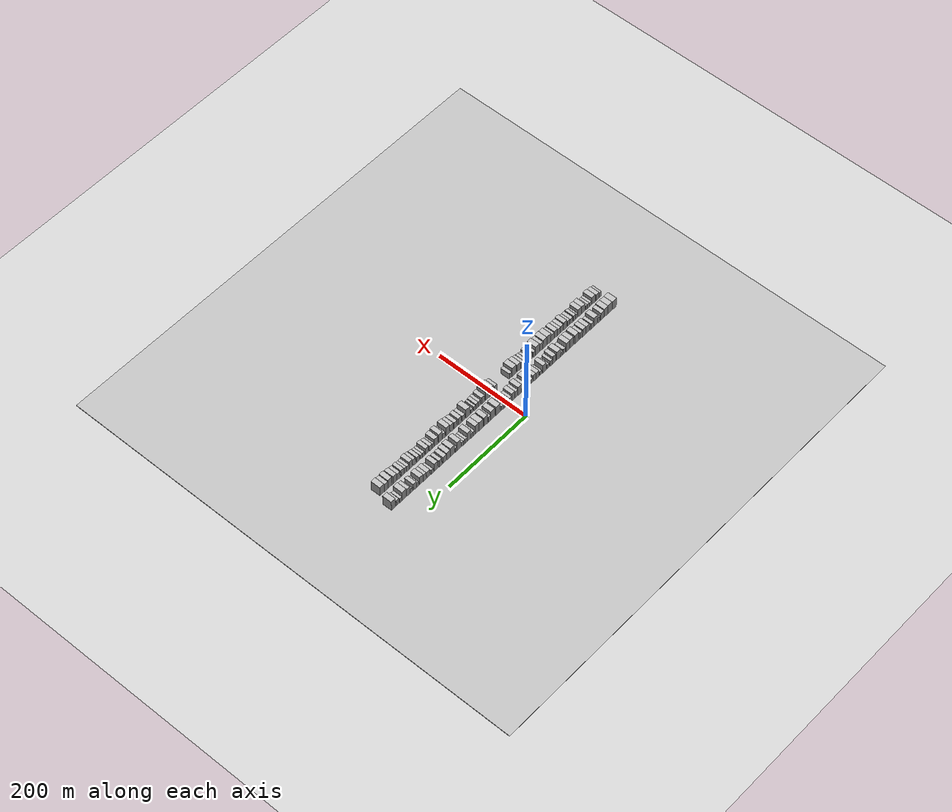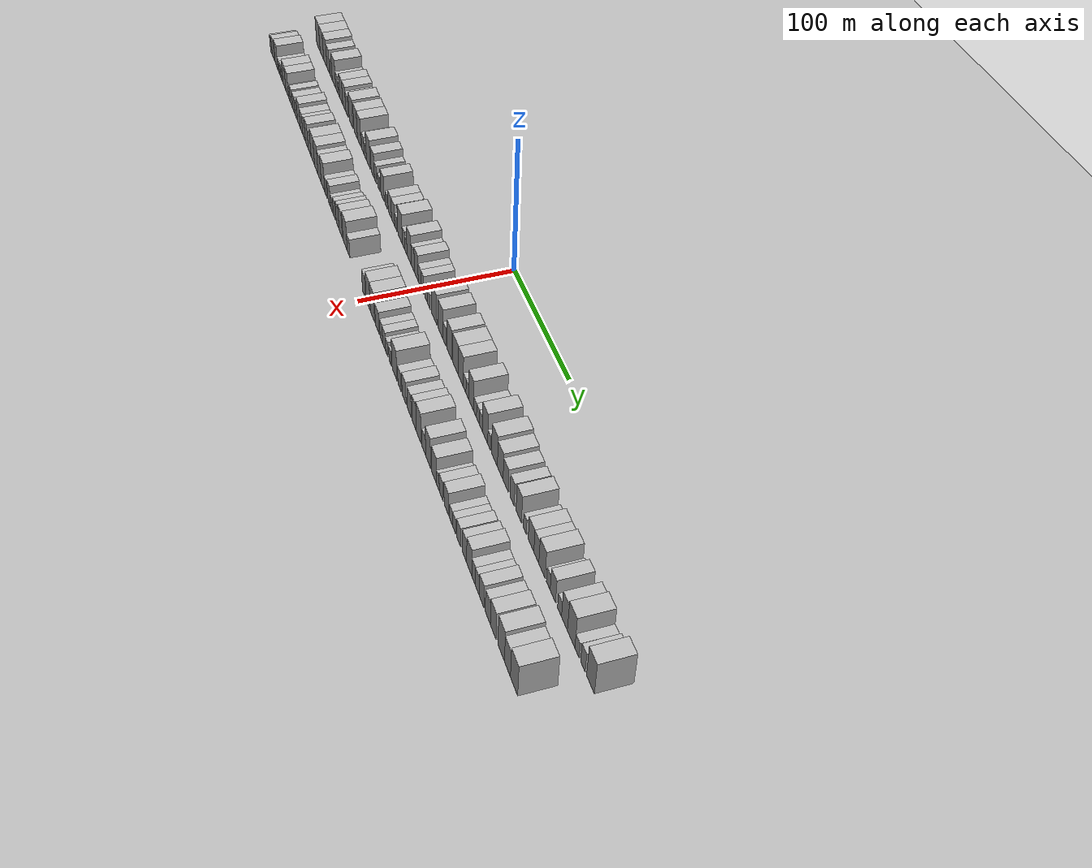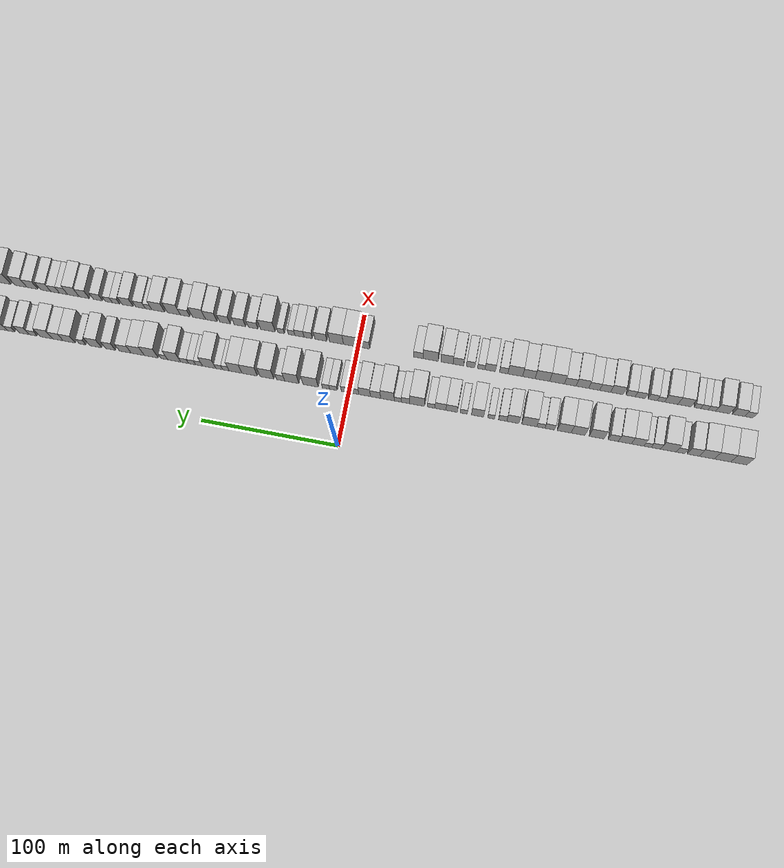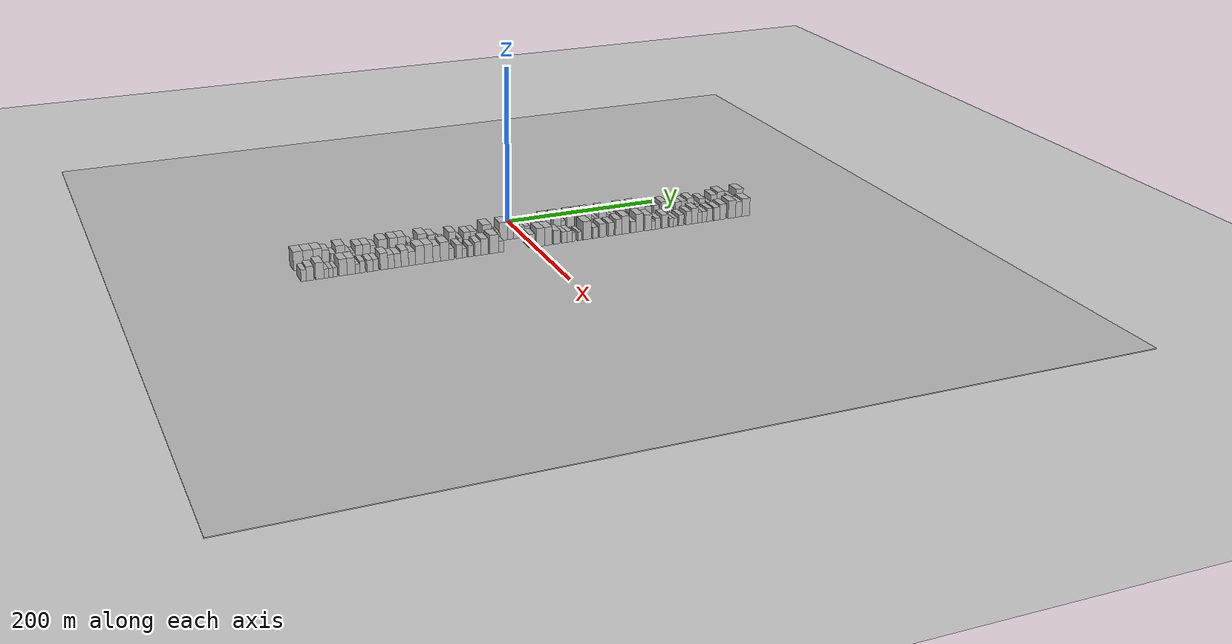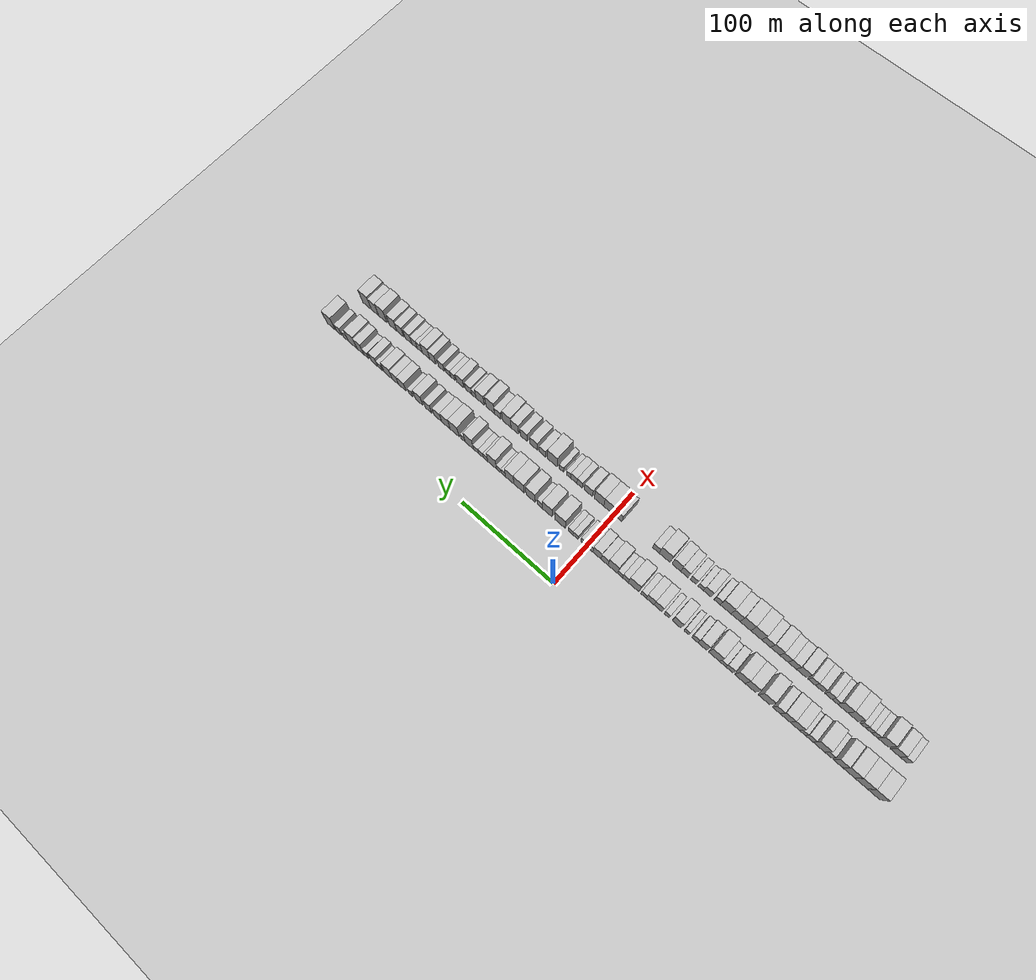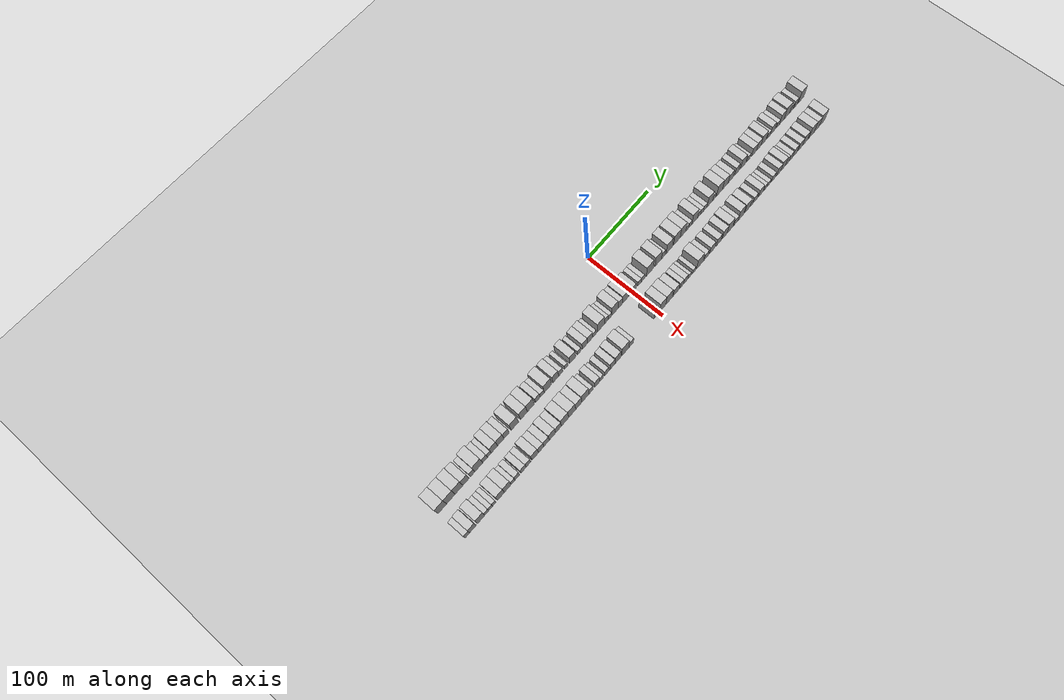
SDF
<?xml version="1.0" encoding="utf-8"?>

<sdf version="1.6">

   <world name="default">

      <gui fullscreen="0">

         <camera name="user_camera">

            <pose>-15 0 4.57585 0 0 0</pose>

            <view_controller>orbit</view_controller>

         </camera>

      </gui>

      <scene>

         <sky>

           <clouds>

             <speed>12</speed>

           </clouds>

         </sky>

         <ambient>0.4 0.4 0.4 1</ambient>

         <background>0.7 0.7 0.7 1</background>

         <shadows>1</shadows>

      </scene>

      <gravity>0 0 -9.8066</gravity>

      <magnetic_field>6e-06 2.3e-05 -4.2e-05</magnetic_field>

      <physics default="0" name="default_physics" type="ode">

         <ode>

            <solver>

               <type>quick</type>

               <iters>10</iters>

               <sor>1.0</sor>

               <use_dynamic_moi_rescaling>0</use_dynamic_moi_rescaling>

            </solver>

            <constraints>

               <cfm>0</cfm>

               <erp>0.2</erp>

               <contact_max_correcting_vel>100</contact_max_correcting_vel>

               <contact_surface_layer>0.001</contact_surface_layer>

            </constraints>

         </ode>

         <max_step_size>0.004</max_step_size>

         <real_time_factor>1</real_time_factor>

         <real_time_update_rate>250</real_time_update_rate>

      </physics>

      <light name="sun" type="directional">

         <cast_shadows>1</cast_shadows>

         <pose>0 0 10 0 0 0</pose>

         <diffuse>0.8 0.8 0.8 1</diffuse>

         <specular>0.2 0.2 0.2 1</specular>

         <attenuation>

            <range>1000</range>

            <constant>0.9</constant>

            <linear>0.01</linear>

            <quadratic>0.001</quadratic>

         </attenuation>

         <direction>-0.5 0.1 -0.9</direction>

      </light>

      <include>

         <name>ground_plane_1</name>

         <uri>model://HANNAS_ground_plane</uri>

         <pose>0 0 0  0 0 0</pose>

      </include>

      <include>

         <name>ground_plane_2</name>

         <uri>model://HANNAS_ground_plane</uri>

         <pose>100 0 0  0 0 0</pose>

      </include>

      <model name="building_1">

         <static>1</static>

         <pose frame="">50.0000 -284.1602 0 0.000000 0.000000 0.000000</pose>

         <link name="link">

            <pose frame="">0 0 12.00 0 0 0</pose>

            <collision name="collision">

               <geometry>

                  <box>

                     <size>20.0000 11.6795 24.0000</size>

                  </box>

               </geometry>

               <max_contacts>10</max_contacts>

               <surface>

                  <contact>

                     <ode/>

                  </contact>

                  <bounce/>

                  <friction>

                     <torsional>

                        <ode/>

                     </torsional>

                     <ode/>

                  </friction>

               </surface>

            </collision>

            <visual name="visual">

               <cast_shadows>0</cast_shadows>

               <geometry>

                  <box>

                     <size>20.0000 11.6795 24.0000</size>

                  </box>

               </geometry>

               <material>

                  <script>

                     <uri>model://HANNAS_wall/materials/scripts</uri>

                     <uri>model://HANNAS_wall/materials/textures</uri>

                     <name>vrc/HANNAS_wall</name>

                  </script>

               </material>

            </visual>

            <self_collide>0</self_collide>

            <enable_wind>0</enable_wind>

            <kinematic>0</kinematic>

         </link>

      </model>

      <model name="building_2">

         <static>1</static>

         <pose frame="">50.0000 -272.4038 0 0.000000 0.000000 0.000000</pose>

         <link name="link">

            <pose frame="">0 0 12.00 0 0 0</pose>

            <collision name="collision">

               <geometry>

                  <box>

                     <size>20.0000 11.8333 24.0000</size>

                  </box>

               </geometry>

               <max_contacts>10</max_contacts>

               <surface>

                  <contact>

                     <ode/>

                  </contact>

                  <bounce/>

                  <friction>

                     <torsional>

                        <ode/>

                     </torsional>

                     <ode/>

                  </friction>

               </surface>

            </collision>

            <visual name="visual">

               <cast_shadows>0</cast_shadows>

               <geometry>

                  <box>

                     <size>20.0000 11.8333 24.0000</size>

                  </box>

               </geometry>

               <material>

                  <script>

                     <uri>model://HANNAS_wall/materials/scripts</uri>

                     <uri>model://HANNAS_wall/materials/textures</uri>

                     <name>vrc/HANNAS_wall</name>

                  </script>

               </material>

            </visual>

            <self_collide>0</self_collide>

            <enable_wind>0</enable_wind>

            <kinematic>0</kinematic>

         </link>

      </model>

      <model name="building_3">

         <static>1</static>

         <pose frame="">50.0000 -261.0836 0 0.000000 0.000000 0.000000</pose>

         <link name="link">

            <pose frame="">0 0 12.00 0 0 0</pose>

            <collision name="collision">

               <geometry>

                  <box>

                     <size>20.0000 10.8070 24.0000</size>

                  </box>

               </geometry>

               <max_contacts>10</max_contacts>

               <surface>

                  <contact>

                     <ode/>

                  </contact>

                  <bounce/>

                  <friction>

                     <torsional>

                        <ode/>

                     </torsional>

                     <ode/>

                  </friction>

               </surface>

            </collision>

            <visual name="visual">

               <cast_shadows>0</cast_shadows>

               <geometry>

                  <box>

                     <size>20.0000 10.8070 24.0000</size>

                  </box>

               </geometry>

               <material>

                  <script>

                     <uri>model://HANNAS_wall/materials/scripts</uri>

                     <uri>model://HANNAS_wall/materials/textures</uri>

                     <name>vrc/HANNAS_wall</name>

                  </script>

               </material>

            </visual>

            <self_collide>0</self_collide>

            <enable_wind>0</enable_wind>

            <kinematic>0</kinematic>

         </link>

      </model>

      <model name="building_4">

         <static>1</static>

         <pose frame="">50.0000 -251.3579 0 0.000000 0.000000 0.000000</pose>

         <link name="link">

            <pose frame="">0 0 10.50 0 0 0</pose>

            <collision name="collision">

               <geometry>

                  <box>

                     <size>20.0000 8.6444 21.0000</size>

                  </box>

               </geometry>

               <max_contacts>10</max_contacts>

               <surface>

                  <contact>

                     <ode/>

                  </contact>

                  <bounce/>

                  <friction>

                     <torsional>

                        <ode/>

                     </torsional>

                     <ode/>

                  </friction>

               </surface>

            </collision>

            <visual name="visual">

               <cast_shadows>0</cast_shadows>

               <geometry>

                  <box>

                     <size>20.0000 8.6444 21.0000</size>

                  </box>

               </geometry>

               <material>

                  <script>

                     <uri>model://HANNAS_wall/materials/scripts</uri>

                     <uri>model://HANNAS_wall/materials/textures</uri>

                     <name>vrc/HANNAS_wall</name>

                  </script>

               </material>

            </visual>

            <self_collide>0</self_collide>

            <enable_wind>0</enable_wind>

            <kinematic>0</kinematic>

         </link>

      </model>

      <model name="building_5">

         <static>1</static>

         <pose frame="">50.0000 -241.9757 0 0.000000 0.000000 0.000000</pose>

         <link name="link">

            <pose frame="">0 0 7.50 0 0 0</pose>

            <collision name="collision">

               <geometry>

                  <box>

                     <size>20.0000 6.1200 15.0000</size>

                  </box>

               </geometry>

               <max_contacts>10</max_contacts>

               <surface>

                  <contact>

                     <ode/>

                  </contact>

                  <bounce/>

                  <friction>

                     <torsional>

                        <ode/>

                     </torsional>

                     <ode/>

                  </friction>

               </surface>

            </collision>

            <visual name="visual">

               <cast_shadows>0</cast_shadows>

               <geometry>

                  <box>

                     <size>20.0000 6.1200 15.0000</size>

                  </box>

               </geometry>

               <material>

                  <script>

                     <uri>model://HANNAS_wall/materials/scripts</uri>

                     <uri>model://HANNAS_wall/materials/textures</uri>

                     <name>vrc/HANNAS_wall</name>

                  </script>

               </material>

            </visual>

            <self_collide>0</self_collide>

            <enable_wind>0</enable_wind>

            <kinematic>0</kinematic>

         </link>

      </model>

      <model name="building_6">

         <static>1</static>

         <pose frame="">50.0000 -233.3348 0 0.000000 0.000000 0.000000</pose>

         <link name="link">

            <pose frame="">0 0 12.00 0 0 0</pose>

            <collision name="collision">

               <geometry>

                  <box>

                     <size>20.0000 11.1619 24.0000</size>

                  </box>

               </geometry>

               <max_contacts>10</max_contacts>

               <surface>

                  <contact>

                     <ode/>

                  </contact>

                  <bounce/>

                  <friction>

                     <torsional>

                        <ode/>

                     </torsional>

                     <ode/>

                  </friction>

               </surface>

            </collision>

            <visual name="visual">

               <cast_shadows>0</cast_shadows>

               <geometry>

                  <box>

                     <size>20.0000 11.1619 24.0000</size>

                  </box>

               </geometry>

               <material>

                  <script>

                     <uri>model://HANNAS_wall/materials/scripts</uri>

                     <uri>model://HANNAS_wall/materials/textures</uri>

                     <name>vrc/HANNAS_wall</name>

                  </script>

               </material>

            </visual>

            <self_collide>0</self_collide>

            <enable_wind>0</enable_wind>

            <kinematic>0</kinematic>

         </link>

      </model>

      <model name="building_7">

         <static>1</static>

         <pose frame="">50.0000 -224.3012 0 0.000000 0.000000 0.000000</pose>

         <link name="link">

            <pose frame="">0 0 7.50 0 0 0</pose>

            <collision name="collision">

               <geometry>

                  <box>

                     <size>20.0000 6.9053 15.0000</size>

                  </box>

               </geometry>

               <max_contacts>10</max_contacts>

               <surface>

                  <contact>

                     <ode/>

                  </contact>

                  <bounce/>

                  <friction>

                     <torsional>

                        <ode/>

                     </torsional>

                     <ode/>

                  </friction>

               </surface>

            </collision>

            <visual name="visual">

               <cast_shadows>0</cast_shadows>

               <geometry>

                  <box>

                     <size>20.0000 6.9053 15.0000</size>

                  </box>

               </geometry>

               <material>

                  <script>

                     <uri>model://HANNAS_wall/materials/scripts</uri>

                     <uri>model://HANNAS_wall/materials/textures</uri>

                     <name>vrc/HANNAS_wall</name>

                  </script>

               </material>

            </visual>

            <self_collide>0</self_collide>

            <enable_wind>0</enable_wind>

            <kinematic>0</kinematic>

         </link>

      </model>

      <model name="building_8">

         <static>1</static>

         <pose frame="">50.0000 -218.1697 0 0.000000 0.000000 0.000000</pose>

         <link name="link">

            <pose frame="">0 0 6.00 0 0 0</pose>

            <collision name="collision">

               <geometry>

                  <box>

                     <size>20.0000 5.3576 12.0000</size>

                  </box>

               </geometry>

               <max_contacts>10</max_contacts>

               <surface>

                  <contact>

                     <ode/>

                  </contact>

                  <bounce/>

                  <friction>

                     <torsional>

                        <ode/>

                     </torsional>

                     <ode/>

                  </friction>

               </surface>

            </collision>

            <visual name="visual">

               <cast_shadows>0</cast_shadows>

               <geometry>

                  <box>

                     <size>20.0000 5.3576 12.0000</size>

                  </box>

               </geometry>

               <material>

                  <script>

                     <uri>model://HANNAS_wall/materials/scripts</uri>

                     <uri>model://HANNAS_wall/materials/textures</uri>

                     <name>vrc/HANNAS_wall</name>

                  </script>

               </material>

            </visual>

            <self_collide>0</self_collide>

            <enable_wind>0</enable_wind>

            <kinematic>0</kinematic>

         </link>

      </model>

      <model name="building_9">

         <static>1</static>

         <pose frame="">50.0000 -210.9690 0 0.000000 0.000000 0.000000</pose>

         <link name="link">

            <pose frame="">0 0 10.50 0 0 0</pose>

            <collision name="collision">

               <geometry>

                  <box>

                     <size>20.0000 9.0439 21.0000</size>

                  </box>

               </geometry>

               <max_contacts>10</max_contacts>

               <surface>

                  <contact>

                     <ode/>

                  </contact>

                  <bounce/>

                  <friction>

                     <torsional>

                        <ode/>

                     </torsional>

                     <ode/>

                  </friction>

               </surface>

            </collision>

            <visual name="visual">

               <cast_shadows>0</cast_shadows>

               <geometry>

                  <box>

                     <size>20.0000 9.0439 21.0000</size>

                  </box>

               </geometry>

               <material>

                  <script>

                     <uri>model://HANNAS_wall/materials/scripts</uri>

                     <uri>model://HANNAS_wall/materials/textures</uri>

                     <name>vrc/HANNAS_wall</name>

                  </script>

               </material>

            </visual>

            <self_collide>0</self_collide>

            <enable_wind>0</enable_wind>

            <kinematic>0</kinematic>

         </link>

      </model>

      <model name="building_10">

         <static>1</static>

         <pose frame="">50.0000 -201.7612 0 0.000000 0.000000 0.000000</pose>

         <link name="link">

            <pose frame="">0 0 10.50 0 0 0</pose>

            <collision name="collision">

               <geometry>

                  <box>

                     <size>20.0000 9.3718 21.0000</size>

                  </box>

               </geometry>

               <max_contacts>10</max_contacts>

               <surface>

                  <contact>

                     <ode/>

                  </contact>

                  <bounce/>

                  <friction>

                     <torsional>

                        <ode/>

                     </torsional>

                     <ode/>

                  </friction>

               </surface>

            </collision>

            <visual name="visual">

               <cast_shadows>0</cast_shadows>

               <geometry>

                  <box>

                     <size>20.0000 9.3718 21.0000</size>

                  </box>

               </geometry>

               <material>

                  <script>

                     <uri>model://HANNAS_wall/materials/scripts</uri>

                     <uri>model://HANNAS_wall/materials/textures</uri>

                     <name>vrc/HANNAS_wall</name>

                  </script>

               </material>

            </visual>

            <self_collide>0</self_collide>

            <enable_wind>0</enable_wind>

            <kinematic>0</kinematic>

         </link>

      </model>

      <model name="building_11">

         <static>1</static>

         <pose frame="">50.0000 -193.3830 0 0.000000 0.000000 0.000000</pose>

         <link name="link">

            <pose frame="">0 0 9.00 0 0 0</pose>

            <collision name="collision">

               <geometry>

                  <box>

                     <size>20.0000 7.3846 18.0000</size>

                  </box>

               </geometry>

               <max_contacts>10</max_contacts>

               <surface>

                  <contact>

                     <ode/>

                  </contact>

                  <bounce/>

                  <friction>

                     <torsional>

                        <ode/>

                     </torsional>

                     <ode/>

                  </friction>

               </surface>

            </collision>

            <visual name="visual">

               <cast_shadows>0</cast_shadows>

               <geometry>

                  <box>

                     <size>20.0000 7.3846 18.0000</size>

                  </box>

               </geometry>

               <material>

                  <script>

                     <uri>model://HANNAS_wall/materials/scripts</uri>

                     <uri>model://HANNAS_wall/materials/textures</uri>

                     <name>vrc/HANNAS_wall</name>

                  </script>

               </material>

            </visual>

            <self_collide>0</self_collide>

            <enable_wind>0</enable_wind>

            <kinematic>0</kinematic>

         </link>

      </model>

      <model name="building_12">

         <static>1</static>

         <pose frame="">50.0000 -181.2933 0 0.000000 0.000000 0.000000</pose>

         <link name="link">

            <pose frame="">0 0 12.00 0 0 0</pose>

            <collision name="collision">

               <geometry>

                  <box>

                     <size>20.0000 10.7947 24.0000</size>

                  </box>

               </geometry>

               <max_contacts>10</max_contacts>

               <surface>

                  <contact>

                     <ode/>

                  </contact>

                  <bounce/>

                  <friction>

                     <torsional>

                        <ode/>

                     </torsional>

                     <ode/>

                  </friction>

               </surface>

            </collision>

            <visual name="visual">

               <cast_shadows>0</cast_shadows>

               <geometry>

                  <box>

                     <size>20.0000 10.7947 24.0000</size>

                  </box>

               </geometry>

               <material>

                  <script>

                     <uri>model://HANNAS_wall/materials/scripts</uri>

                     <uri>model://HANNAS_wall/materials/textures</uri>

                     <name>vrc/HANNAS_wall</name>

                  </script>

               </material>

            </visual>

            <self_collide>0</self_collide>

            <enable_wind>0</enable_wind>

            <kinematic>0</kinematic>

         </link>

      </model>

      <model name="building_13">

         <static>1</static>

         <pose frame="">50.0000 -167.8822 0 0.000000 0.000000 0.000000</pose>

         <link name="link">

            <pose frame="">0 0 12.00 0 0 0</pose>

            <collision name="collision">

               <geometry>

                  <box>

                     <size>20.0000 10.0277 24.0000</size>

                  </box>

               </geometry>

               <max_contacts>10</max_contacts>

               <surface>

                  <contact>

                     <ode/>

                  </contact>

                  <bounce/>

                  <friction>

                     <torsional>

                        <ode/>

                     </torsional>

                     <ode/>

                  </friction>

               </surface>

            </collision>

            <visual name="visual">

               <cast_shadows>0</cast_shadows>

               <geometry>

                  <box>

                     <size>20.0000 10.0277 24.0000</size>

                  </box>

               </geometry>

               <material>

                  <script>

                     <uri>model://HANNAS_wall/materials/scripts</uri>

                     <uri>model://HANNAS_wall/materials/textures</uri>

                     <name>vrc/HANNAS_wall</name>

                  </script>

               </material>

            </visual>

            <self_collide>0</self_collide>

            <enable_wind>0</enable_wind>

            <kinematic>0</kinematic>

         </link>

      </model>

      <model name="building_14">

         <static>1</static>

         <pose frame="">50.0000 -157.8020 0 0.000000 0.000000 0.000000</pose>

         <link name="link">

            <pose frame="">0 0 12.00 0 0 0</pose>

            <collision name="collision">

               <geometry>

                  <box>

                     <size>20.0000 10.1326 24.0000</size>

                  </box>

               </geometry>

               <max_contacts>10</max_contacts>

               <surface>

                  <contact>

                     <ode/>

                  </contact>

                  <bounce/>

                  <friction>

                     <torsional>

                        <ode/>

                     </torsional>

                     <ode/>

                  </friction>

               </surface>

            </collision>

            <visual name="visual">

               <cast_shadows>0</cast_shadows>

               <geometry>

                  <box>

                     <size>20.0000 10.1326 24.0000</size>

                  </box>

               </geometry>

               <material>

                  <script>

                     <uri>model://HANNAS_wall/materials/scripts</uri>

                     <uri>model://HANNAS_wall/materials/textures</uri>

                     <name>vrc/HANNAS_wall</name>

                  </script>

               </material>

            </visual>

            <self_collide>0</self_collide>

            <enable_wind>0</enable_wind>

            <kinematic>0</kinematic>

         </link>

      </model>

      <model name="building_15">

         <static>1</static>

         <pose frame="">50.0000 -147.2319 0 0.000000 0.000000 0.000000</pose>

         <link name="link">

            <pose frame="">0 0 7.50 0 0 0</pose>

            <collision name="collision">

               <geometry>

                  <box>

                     <size>20.0000 7.0075 15.0000</size>

                  </box>

               </geometry>

               <max_contacts>10</max_contacts>

               <surface>

                  <contact>

                     <ode/>

                  </contact>

                  <bounce/>

                  <friction>

                     <torsional>

                        <ode/>

                     </torsional>

                     <ode/>

                  </friction>

               </surface>

            </collision>

            <visual name="visual">

               <cast_shadows>0</cast_shadows>

               <geometry>

                  <box>

                     <size>20.0000 7.0075 15.0000</size>

                  </box>

               </geometry>

               <material>

                  <script>

                     <uri>model://HANNAS_wall/materials/scripts</uri>

                     <uri>model://HANNAS_wall/materials/textures</uri>

                     <name>vrc/HANNAS_wall</name>

                  </script>

               </material>

            </visual>

            <self_collide>0</self_collide>

            <enable_wind>0</enable_wind>

            <kinematic>0</kinematic>

         </link>

      </model>

      <model name="building_16">

         <static>1</static>

         <pose frame="">50.0000 -140.7398 0 0.000000 0.000000 0.000000</pose>

         <link name="link">

            <pose frame="">0 0 6.00 0 0 0</pose>

            <collision name="collision">

               <geometry>

                  <box>

                     <size>20.0000 5.9767 12.0000</size>

                  </box>

               </geometry>

               <max_contacts>10</max_contacts>

               <surface>

                  <contact>

                     <ode/>

                  </contact>

                  <bounce/>

                  <friction>

                     <torsional>

                        <ode/>

                     </torsional>

                     <ode/>

                  </friction>

               </surface>

            </collision>

            <visual name="visual">

               <cast_shadows>0</cast_shadows>

               <geometry>

                  <box>

                     <size>20.0000 5.9767 12.0000</size>

                  </box>

               </geometry>

               <material>

                  <script>

                     <uri>model://HANNAS_wall/materials/scripts</uri>

                     <uri>model://HANNAS_wall/materials/textures</uri>

                     <name>vrc/HANNAS_wall</name>

                  </script>

               </material>

            </visual>

            <self_collide>0</self_collide>

            <enable_wind>0</enable_wind>

            <kinematic>0</kinematic>

         </link>

      </model>

      <model name="building_17">

         <static>1</static>

         <pose frame="">50.0000 -132.2860 0 0.000000 0.000000 0.000000</pose>

         <link name="link">

            <pose frame="">0 0 12.00 0 0 0</pose>

            <collision name="collision">

               <geometry>

                  <box>

                     <size>20.0000 10.9309 24.0000</size>

                  </box>

               </geometry>

               <max_contacts>10</max_contacts>

               <surface>

                  <contact>

                     <ode/>

                  </contact>

                  <bounce/>

                  <friction>

                     <torsional>

                        <ode/>

                     </torsional>

                     <ode/>

                  </friction>

               </surface>

            </collision>

            <visual name="visual">

               <cast_shadows>0</cast_shadows>

               <geometry>

                  <box>

                     <size>20.0000 10.9309 24.0000</size>

                  </box>

               </geometry>

               <material>

                  <script>

                     <uri>model://HANNAS_wall/materials/scripts</uri>

                     <uri>model://HANNAS_wall/materials/textures</uri>

                     <name>vrc/HANNAS_wall</name>

                  </script>

               </material>

            </visual>

            <self_collide>0</self_collide>

            <enable_wind>0</enable_wind>

            <kinematic>0</kinematic>

         </link>

      </model>

      <model name="building_18">

         <static>1</static>

         <pose frame="">50.0000 -120.3710 0 0.000000 0.000000 0.000000</pose>

         <link name="link">

            <pose frame="">0 0 10.50 0 0 0</pose>

            <collision name="collision">

               <geometry>

                  <box>

                     <size>20.0000 8.8991 21.0000</size>

                  </box>

               </geometry>

               <max_contacts>10</max_contacts>

               <surface>

                  <contact>

                     <ode/>

                  </contact>

                  <bounce/>

                  <friction>

                     <torsional>

                        <ode/>

                     </torsional>

                     <ode/>

                  </friction>

               </surface>

            </collision>

            <visual name="visual">

               <cast_shadows>0</cast_shadows>

               <geometry>

                  <box>

                     <size>20.0000 8.8991 21.0000</size>

                  </box>

               </geometry>

               <material>

                  <script>

                     <uri>model://HANNAS_wall/materials/scripts</uri>

                     <uri>model://HANNAS_wall/materials/textures</uri>

                     <name>vrc/HANNAS_wall</name>

                  </script>

               </material>

            </visual>

            <self_collide>0</self_collide>

            <enable_wind>0</enable_wind>

            <kinematic>0</kinematic>

         </link>

      </model>

      <model name="building_19">

         <static>1</static>

         <pose frame="">50.0000 -112.9033 0 0.000000 0.000000 0.000000</pose>

         <link name="link">

            <pose frame="">0 0 7.50 0 0 0</pose>

            <collision name="collision">

               <geometry>

                  <box>

                     <size>20.0000 6.0361 15.0000</size>

                  </box>

               </geometry>

               <max_contacts>10</max_contacts>

               <surface>

                  <contact>

                     <ode/>

                  </contact>

                  <bounce/>

                  <friction>

                     <torsional>

                        <ode/>

                     </torsional>

                     <ode/>

                  </friction>

               </surface>

            </collision>

            <visual name="visual">

               <cast_shadows>0</cast_shadows>

               <geometry>

                  <box>

                     <size>20.0000 6.0361 15.0000</size>

                  </box>

               </geometry>

               <material>

                  <script>

                     <uri>model://HANNAS_wall/materials/scripts</uri>

                     <uri>model://HANNAS_wall/materials/textures</uri>

                     <name>vrc/HANNAS_wall</name>

                  </script>

               </material>

            </visual>

            <self_collide>0</self_collide>

            <enable_wind>0</enable_wind>

            <kinematic>0</kinematic>

         </link>

      </model>

      <model name="building_20">

         <static>1</static>

         <pose frame="">50.0000 -104.4602 0 0.000000 0.000000 0.000000</pose>

         <link name="link">

            <pose frame="">0 0 6.00 0 0 0</pose>

            <collision name="collision">

               <geometry>

                  <box>

                     <size>20.0000 4.8501 12.0000</size>

                  </box>

               </geometry>

               <max_contacts>10</max_contacts>

               <surface>

                  <contact>

                     <ode/>

                  </contact>

                  <bounce/>

                  <friction>

                     <torsional>

                        <ode/>

                     </torsional>

                     <ode/>

                  </friction>

               </surface>

            </collision>

            <visual name="visual">

               <cast_shadows>0</cast_shadows>

               <geometry>

                  <box>

                     <size>20.0000 4.8501 12.0000</size>

                  </box>

               </geometry>

               <material>

                  <script>

                     <uri>model://HANNAS_wall/materials/scripts</uri>

                     <uri>model://HANNAS_wall/materials/textures</uri>

                     <name>vrc/HANNAS_wall</name>

                  </script>

               </material>

            </visual>

            <self_collide>0</self_collide>

            <enable_wind>0</enable_wind>

            <kinematic>0</kinematic>

         </link>

      </model>

      <model name="building_21">

         <static>1</static>

         <pose frame="">50.0000 -94.5433 0 0.000000 0.000000 0.000000</pose>

         <link name="link">

            <pose frame="">0 0 10.50 0 0 0</pose>

            <collision name="collision">

               <geometry>

                  <box>

                     <size>20.0000 8.9838 21.0000</size>

                  </box>

               </geometry>

               <max_contacts>10</max_contacts>

               <surface>

                  <contact>

                     <ode/>

                  </contact>

                  <bounce/>

                  <friction>

                     <torsional>

                        <ode/>

                     </torsional>

                     <ode/>

                  </friction>

               </surface>

            </collision>

            <visual name="visual">

               <cast_shadows>0</cast_shadows>

               <geometry>

                  <box>

                     <size>20.0000 8.9838 21.0000</size>

                  </box>

               </geometry>

               <material>

                  <script>

                     <uri>model://HANNAS_wall/materials/scripts</uri>

                     <uri>model://HANNAS_wall/materials/textures</uri>

                     <name>vrc/HANNAS_wall</name>

                  </script>

               </material>

            </visual>

            <self_collide>0</self_collide>

            <enable_wind>0</enable_wind>

            <kinematic>0</kinematic>

         </link>

      </model>

      <model name="building_22">

         <static>1</static>

         <pose frame="">50.0000 -84.4169 0 0.000000 0.000000 0.000000</pose>

         <link name="link">

            <pose frame="">0 0 6.00 0 0 0</pose>

            <collision name="collision">

               <geometry>

                  <box>

                     <size>20.0000 5.2689 12.0000</size>

                  </box>

               </geometry>

               <max_contacts>10</max_contacts>

               <surface>

                  <contact>

                     <ode/>

                  </contact>

                  <bounce/>

                  <friction>

                     <torsional>

                        <ode/>

                     </torsional>

                     <ode/>

                  </friction>

               </surface>

            </collision>

            <visual name="visual">

               <cast_shadows>0</cast_shadows>

               <geometry>

                  <box>

                     <size>20.0000 5.2689 12.0000</size>

                  </box>

               </geometry>

               <material>

                  <script>

                     <uri>model://HANNAS_wall/materials/scripts</uri>

                     <uri>model://HANNAS_wall/materials/textures</uri>

                     <name>vrc/HANNAS_wall</name>

                  </script>

               </material>

            </visual>

            <self_collide>0</self_collide>

            <enable_wind>0</enable_wind>

            <kinematic>0</kinematic>

         </link>

      </model>

      <model name="building_23">

         <static>1</static>

         <pose frame="">50.0000 -75.6403 0 0.000000 0.000000 0.000000</pose>

         <link name="link">

            <pose frame="">0 0 9.00 0 0 0</pose>

            <collision name="collision">

               <geometry>

                  <box>

                     <size>20.0000 8.2843 18.0000</size>

                  </box>

               </geometry>

               <max_contacts>10</max_contacts>

               <surface>

                  <contact>

                     <ode/>

                  </contact>

                  <bounce/>

                  <friction>

                     <torsional>

                        <ode/>

                     </torsional>

                     <ode/>

                  </friction>

               </surface>

            </collision>

            <visual name="visual">

               <cast_shadows>0</cast_shadows>

               <geometry>

                  <box>

                     <size>20.0000 8.2843 18.0000</size>

                  </box>

               </geometry>

               <material>

                  <script>

                     <uri>model://HANNAS_wall/materials/scripts</uri>

                     <uri>model://HANNAS_wall/materials/textures</uri>

                     <name>vrc/HANNAS_wall</name>

                  </script>

               </material>

            </visual>

            <self_collide>0</self_collide>

            <enable_wind>0</enable_wind>

            <kinematic>0</kinematic>

         </link>

      </model>

      <model name="building_24">

         <static>1</static>

         <pose frame="">50.0000 -67.4629 0 0.000000 0.000000 0.000000</pose>

         <link name="link">

            <pose frame="">0 0 9.00 0 0 0</pose>

            <collision name="collision">

               <geometry>

                  <box>

                     <size>20.0000 8.0704 18.0000</size>

                  </box>

               </geometry>

               <max_contacts>10</max_contacts>

               <surface>

                  <contact>

                     <ode/>

                  </contact>

                  <bounce/>

                  <friction>

                     <torsional>

                        <ode/>

                     </torsional>

                     <ode/>

                  </friction>

               </surface>

            </collision>

            <visual name="visual">

               <cast_shadows>0</cast_shadows>

               <geometry>

                  <box>

                     <size>20.0000 8.0704 18.0000</size>

                  </box>

               </geometry>

               <material>

                  <script>

                     <uri>model://HANNAS_wall/materials/scripts</uri>

                     <uri>model://HANNAS_wall/materials/textures</uri>

                     <name>vrc/HANNAS_wall</name>

                  </script>

               </material>

            </visual>

            <self_collide>0</self_collide>

            <enable_wind>0</enable_wind>

            <kinematic>0</kinematic>

         </link>

      </model>

      <model name="building_25">

         <static>1</static>

         <pose frame="">50.0000 -60.5944 0 0.000000 0.000000 0.000000</pose>

         <link name="link">

            <pose frame="">0 0 6.00 0 0 0</pose>

            <collision name="collision">

               <geometry>

                  <box>

                     <size>20.0000 5.6667 12.0000</size>

                  </box>

               </geometry>

               <max_contacts>10</max_contacts>

               <surface>

                  <contact>

                     <ode/>

                  </contact>

                  <bounce/>

                  <friction>

                     <torsional>

                        <ode/>

                     </torsional>

                     <ode/>

                  </friction>

               </surface>

            </collision>

            <visual name="visual">

               <cast_shadows>0</cast_shadows>

               <geometry>

                  <box>

                     <size>20.0000 5.6667 12.0000</size>

                  </box>

               </geometry>

               <material>

                  <script>

                     <uri>model://HANNAS_wall/materials/scripts</uri>

                     <uri>model://HANNAS_wall/materials/textures</uri>

                     <name>vrc/HANNAS_wall</name>

                  </script>

               </material>

            </visual>

            <self_collide>0</self_collide>

            <enable_wind>0</enable_wind>

            <kinematic>0</kinematic>

         </link>

      </model>

      <model name="building_26">

         <static>1</static>

         <pose frame="">50.0000 -50.2685 0 0.000000 0.000000 0.000000</pose>

         <link name="link">

            <pose frame="">0 0 12.00 0 0 0</pose>

            <collision name="collision">

               <geometry>

                  <box>

                     <size>20.0000 10.9852 24.0000</size>

                  </box>

               </geometry>

               <max_contacts>10</max_contacts>

               <surface>

                  <contact>

                     <ode/>

                  </contact>

                  <bounce/>

                  <friction>

                     <torsional>

                        <ode/>

                     </torsional>

                     <ode/>

                  </friction>

               </surface>

            </collision>

            <visual name="visual">

               <cast_shadows>0</cast_shadows>

               <geometry>

                  <box>

                     <size>20.0000 10.9852 24.0000</size>

                  </box>

               </geometry>

               <material>

                  <script>

                     <uri>model://HANNAS_wall/materials/scripts</uri>

                     <uri>model://HANNAS_wall/materials/textures</uri>

                     <name>vrc/HANNAS_wall</name>

                  </script>

               </material>

            </visual>

            <self_collide>0</self_collide>

            <enable_wind>0</enable_wind>

            <kinematic>0</kinematic>

         </link>

      </model>

      <model name="building_27">

         <static>1</static>

         <pose frame="">50.0000 -41.7506 0 0.000000 0.000000 0.000000</pose>

         <link name="link">

            <pose frame="">0 0 7.50 0 0 0</pose>

            <collision name="collision">

               <geometry>

                  <box>

                     <size>20.0000 6.0505 15.0000</size>

                  </box>

               </geometry>

               <max_contacts>10</max_contacts>

               <surface>

                  <contact>

                     <ode/>

                  </contact>

                  <bounce/>

                  <friction>

                     <torsional>

                        <ode/>

                     </torsional>

                     <ode/>

                  </friction>

               </surface>

            </collision>

            <visual name="visual">

               <cast_shadows>0</cast_shadows>

               <geometry>

                  <box>

                     <size>20.0000 6.0505 15.0000</size>

                  </box>

               </geometry>

               <material>

                  <script>

                     <uri>model://HANNAS_wall/materials/scripts</uri>

                     <uri>model://HANNAS_wall/materials/textures</uri>

                     <name>vrc/HANNAS_wall</name>

                  </script>

               </material>

            </visual>

            <self_collide>0</self_collide>

            <enable_wind>0</enable_wind>

            <kinematic>0</kinematic>

         </link>

      </model>

      <model name="building_28">

         <static>1</static>

         <pose frame="">50.0000 -36.0950 0 0.000000 0.000000 0.000000</pose>

         <link name="link">

            <pose frame="">0 0 6.00 0 0 0</pose>

            <collision name="collision">

               <geometry>

                  <box>

                     <size>20.0000 5.2608 12.0000</size>

                  </box>

               </geometry>

               <max_contacts>10</max_contacts>

               <surface>

                  <contact>

                     <ode/>

                  </contact>

                  <bounce/>

                  <friction>

                     <torsional>

                        <ode/>

                     </torsional>

                     <ode/>

                  </friction>

               </surface>

            </collision>

            <visual name="visual">

               <cast_shadows>0</cast_shadows>

               <geometry>

                  <box>

                     <size>20.0000 5.2608 12.0000</size>

                  </box>

               </geometry>

               <material>

                  <script>

                     <uri>model://HANNAS_wall/materials/scripts</uri>

                     <uri>model://HANNAS_wall/materials/textures</uri>

                     <name>vrc/HANNAS_wall</name>

                  </script>

               </material>

            </visual>

            <self_collide>0</self_collide>

            <enable_wind>0</enable_wind>

            <kinematic>0</kinematic>

         </link>

      </model>

      <model name="building_29">

         <static>1</static>

         <pose frame="">50.0000 -28.4472 0 0.000000 0.000000 0.000000</pose>

         <link name="link">

            <pose frame="">0 0 12.00 0 0 0</pose>

            <collision name="collision">

               <geometry>

                  <box>

                     <size>20.0000 10.0347 24.0000</size>

                  </box>

               </geometry>

               <max_contacts>10</max_contacts>

               <surface>

                  <contact>

                     <ode/>

                  </contact>

                  <bounce/>

                  <friction>

                     <torsional>

                        <ode/>

                     </torsional>

                     <ode/>

                  </friction>

               </surface>

            </collision>

            <visual name="visual">

               <cast_shadows>0</cast_shadows>

               <geometry>

                  <box>

                     <size>20.0000 10.0347 24.0000</size>

                  </box>

               </geometry>

               <material>

                  <script>

                     <uri>model://HANNAS_wall/materials/scripts</uri>

                     <uri>model://HANNAS_wall/materials/textures</uri>

                     <name>vrc/HANNAS_wall</name>

                  </script>

               </material>

            </visual>

            <self_collide>0</self_collide>

            <enable_wind>0</enable_wind>

            <kinematic>0</kinematic>

         </link>

      </model>

      <model name="building_30">

         <static>1</static>

         <pose frame="">50.0000 -19.6835 0 0.000000 0.000000 0.000000</pose>

         <link name="link">

            <pose frame="">0 0 9.00 0 0 0</pose>

            <collision name="collision">

               <geometry>

                  <box>

                     <size>20.0000 7.4927 18.0000</size>

                  </box>

               </geometry>

               <max_contacts>10</max_contacts>

               <surface>

                  <contact>

                     <ode/>

                  </contact>

                  <bounce/>

                  <friction>

                     <torsional>

                        <ode/>

                     </torsional>

                     <ode/>

                  </friction>

               </surface>

            </collision>

            <visual name="visual">

               <cast_shadows>0</cast_shadows>

               <geometry>

                  <box>

                     <size>20.0000 7.4927 18.0000</size>

                  </box>

               </geometry>

               <material>

                  <script>

                     <uri>model://HANNAS_wall/materials/scripts</uri>

                     <uri>model://HANNAS_wall/materials/textures</uri>

                     <name>vrc/HANNAS_wall</name>

                  </script>

               </material>

            </visual>

            <self_collide>0</self_collide>

            <enable_wind>0</enable_wind>

            <kinematic>0</kinematic>

         </link>

      </model>

      <model name="building_31">

         <static>1</static>

         <pose frame="">50.0000 -11.6339 0 0.000000 0.000000 0.000000</pose>

         <link name="link">

            <pose frame="">0 0 10.50 0 0 0</pose>

            <collision name="collision">

               <geometry>

                  <box>

                     <size>20.0000 8.6066 21.0000</size>

                  </box>

               </geometry>

               <max_contacts>10</max_contacts>

               <surface>

                  <contact>

                     <ode/>

                  </contact>

                  <bounce/>

                  <friction>

                     <torsional>

                        <ode/>

                     </torsional>

                     <ode/>

                  </friction>

               </surface>

            </collision>

            <visual name="visual">

               <cast_shadows>0</cast_shadows>

               <geometry>

                  <box>

                     <size>20.0000 8.6066 21.0000</size>

                  </box>

               </geometry>

               <material>

                  <script>

                     <uri>model://HANNAS_wall/materials/scripts</uri>

                     <uri>model://HANNAS_wall/materials/textures</uri>

                     <name>vrc/HANNAS_wall</name>

                  </script>

               </material>

            </visual>

            <self_collide>0</self_collide>

            <enable_wind>0</enable_wind>

            <kinematic>0</kinematic>

         </link>

      </model>

      <model name="building_32">

         <static>1</static>

         <pose frame="">50.0000 -4.2705 0 0.000000 0.000000 0.000000</pose>

         <link name="link">

            <pose frame="">0 0 7.50 0 0 0</pose>

            <collision name="collision">

               <geometry>

                  <box>

                     <size>20.0000 6.1202 15.0000</size>

                  </box>

               </geometry>

               <max_contacts>10</max_contacts>

               <surface>

                  <contact>

                     <ode/>

                  </contact>

                  <bounce/>

                  <friction>

                     <torsional>

                        <ode/>

                     </torsional>

                     <ode/>

                  </friction>

               </surface>

            </collision>

            <visual name="visual">

               <cast_shadows>0</cast_shadows>

               <geometry>

                  <box>

                     <size>20.0000 6.1202 15.0000</size>

                  </box>

               </geometry>

               <material>

                  <script>

                     <uri>model://HANNAS_wall/materials/scripts</uri>

                     <uri>model://HANNAS_wall/materials/textures</uri>

                     <name>vrc/HANNAS_wall</name>

                  </script>

               </material>

            </visual>

            <self_collide>0</self_collide>

            <enable_wind>0</enable_wind>

            <kinematic>0</kinematic>

         </link>

      </model>

      <model name="building_33">

         <static>1</static>

         <pose frame="">50.0000 2.1707 0 0.000000 0.000000 0.000000</pose>

         <link name="link">

            <pose frame="">0 0 7.50 0 0 0</pose>

            <collision name="collision">

               <geometry>

                  <box>

                     <size>20.0000 6.7621 15.0000</size>

                  </box>

               </geometry>

               <max_contacts>10</max_contacts>

               <surface>

                  <contact>

                     <ode/>

                  </contact>

                  <bounce/>

                  <friction>

                     <torsional>

                        <ode/>

                     </torsional>

                     <ode/>

                  </friction>

               </surface>

            </collision>

            <visual name="visual">

               <cast_shadows>0</cast_shadows>

               <geometry>

                  <box>

                     <size>20.0000 6.7621 15.0000</size>

                  </box>

               </geometry>

               <material>

                  <script>

                     <uri>model://HANNAS_wall/materials/scripts</uri>

                     <uri>model://HANNAS_wall/materials/textures</uri>

                     <name>vrc/HANNAS_wall</name>

                  </script>

               </material>

            </visual>

            <self_collide>0</self_collide>

            <enable_wind>0</enable_wind>

            <kinematic>0</kinematic>

         </link>

      </model>

      <model name="building_34">

         <static>1</static>

         <pose frame="">50.0000 11.3781 0 0.000000 0.000000 0.000000</pose>

         <link name="link">

            <pose frame="">0 0 6.00 0 0 0</pose>

            <collision name="collision">

               <geometry>

                  <box>

                     <size>20.0000 5.6528 12.0000</size>

                  </box>

               </geometry>

               <max_contacts>10</max_contacts>

               <surface>

                  <contact>

                     <ode/>

                  </contact>

                  <bounce/>

                  <friction>

                     <torsional>

                        <ode/>

                     </torsional>

                     <ode/>

                  </friction>

               </surface>

            </collision>

            <visual name="visual">

               <cast_shadows>0</cast_shadows>

               <geometry>

                  <box>

                     <size>20.0000 5.6528 12.0000</size>

                  </box>

               </geometry>

               <material>

                  <script>

                     <uri>model://HANNAS_wall/materials/scripts</uri>

                     <uri>model://HANNAS_wall/materials/textures</uri>

                     <name>vrc/HANNAS_wall</name>

                  </script>

               </material>

            </visual>

            <self_collide>0</self_collide>

            <enable_wind>0</enable_wind>

            <kinematic>0</kinematic>

         </link>

      </model>

      <model name="building_35">

         <static>1</static>

         <pose frame="">50.0000 16.8766 0 0.000000 0.000000 0.000000</pose>

         <link name="link">

            <pose frame="">0 0 6.00 0 0 0</pose>

            <collision name="collision">

               <geometry>

                  <box>

                     <size>20.0000 5.3441 12.0000</size>

                  </box>

               </geometry>

               <max_contacts>10</max_contacts>

               <surface>

                  <contact>

                     <ode/>

                  </contact>

                  <bounce/>

                  <friction>

                     <torsional>

                        <ode/>

                     </torsional>

                     <ode/>

                  </friction>

               </surface>

            </collision>

            <visual name="visual">

               <cast_shadows>0</cast_shadows>

               <geometry>

                  <box>

                     <size>20.0000 5.3441 12.0000</size>

                  </box>

               </geometry>

               <material>

                  <script>

                     <uri>model://HANNAS_wall/materials/scripts</uri>

                     <uri>model://HANNAS_wall/materials/textures</uri>

                     <name>vrc/HANNAS_wall</name>

                  </script>

               </material>

            </visual>

            <self_collide>0</self_collide>

            <enable_wind>0</enable_wind>

            <kinematic>0</kinematic>

         </link>

      </model>

      <model name="building_36">

         <static>1</static>

         <pose frame="">50.0000 28.2322 0 0.000000 0.000000 0.000000</pose>

         <link name="link">

            <pose frame="">0 0 12.00 0 0 0</pose>

            <collision name="collision">

               <geometry>

                  <box>

                     <size>20.0000 11.3671 24.0000</size>

                  </box>

               </geometry>

               <max_contacts>10</max_contacts>

               <surface>

                  <contact>

                     <ode/>

                  </contact>

                  <bounce/>

                  <friction>

                     <torsional>

                        <ode/>

                     </torsional>

                     <ode/>

                  </friction>

               </surface>

            </collision>

            <visual name="visual">

               <cast_shadows>0</cast_shadows>

               <geometry>

                  <box>

                     <size>20.0000 11.3671 24.0000</size>

                  </box>

               </geometry>

               <material>

                  <script>

                     <uri>model://HANNAS_wall/materials/scripts</uri>

                     <uri>model://HANNAS_wall/materials/textures</uri>

                     <name>vrc/HANNAS_wall</name>

                  </script>

               </material>

            </visual>

            <self_collide>0</self_collide>

            <enable_wind>0</enable_wind>

            <kinematic>0</kinematic>

         </link>

      </model>

      <model name="building_37">

         <static>1</static>

         <pose frame="">50.0000 42.1491 0 0.000000 0.000000 0.000000</pose>

         <link name="link">

            <pose frame="">0 0 12.00 0 0 0</pose>

            <collision name="collision">

               <geometry>

                  <box>

                     <size>20.0000 10.4667 24.0000</size>

                  </box>

               </geometry>

               <max_contacts>10</max_contacts>

               <surface>

                  <contact>

                     <ode/>

                  </contact>

                  <bounce/>

                  <friction>

                     <torsional>

                        <ode/>

                     </torsional>

                     <ode/>

                  </friction>

               </surface>

            </collision>

            <visual name="visual">

               <cast_shadows>0</cast_shadows>

               <geometry>

                  <box>

                     <size>20.0000 10.4667 24.0000</size>

                  </box>

               </geometry>

               <material>

                  <script>

                     <uri>model://HANNAS_wall/materials/scripts</uri>

                     <uri>model://HANNAS_wall/materials/textures</uri>

                     <name>vrc/HANNAS_wall</name>

                  </script>

               </material>

            </visual>

            <self_collide>0</self_collide>

            <enable_wind>0</enable_wind>

            <kinematic>0</kinematic>

         </link>

      </model>

      <model name="building_38">

         <static>1</static>

         <pose frame="">50.0000 50.3869 0 0.000000 0.000000 0.000000</pose>

         <link name="link">

            <pose frame="">0 0 7.50 0 0 0</pose>

            <collision name="collision">

               <geometry>

                  <box>

                     <size>20.0000 6.0088 15.0000</size>

                  </box>

               </geometry>

               <max_contacts>10</max_contacts>

               <surface>

                  <contact>

                     <ode/>

                  </contact>

                  <bounce/>

                  <friction>

                     <torsional>

                        <ode/>

                     </torsional>

                     <ode/>

                  </friction>

               </surface>

            </collision>

            <visual name="visual">

               <cast_shadows>0</cast_shadows>

               <geometry>

                  <box>

                     <size>20.0000 6.0088 15.0000</size>

                  </box>

               </geometry>

               <material>

                  <script>

                     <uri>model://HANNAS_wall/materials/scripts</uri>

                     <uri>model://HANNAS_wall/materials/textures</uri>

                     <name>vrc/HANNAS_wall</name>

                  </script>

               </material>

            </visual>

            <self_collide>0</self_collide>

            <enable_wind>0</enable_wind>

            <kinematic>0</kinematic>

         </link>

      </model>

      <model name="building_39">

         <static>1</static>

         <pose frame="">50.0000 60.5016 0 0.000000 0.000000 0.000000</pose>

         <link name="link">

            <pose frame="">0 0 12.00 0 0 0</pose>

            <collision name="collision">

               <geometry>

                  <box>

                     <size>20.0000 10.2207 24.0000</size>

                  </box>

               </geometry>

               <max_contacts>10</max_contacts>

               <surface>

                  <contact>

                     <ode/>

                  </contact>

                  <bounce/>

                  <friction>

                     <torsional>

                        <ode/>

                     </torsional>

                     <ode/>

                  </friction>

               </surface>

            </collision>

            <visual name="visual">

               <cast_shadows>0</cast_shadows>

               <geometry>

                  <box>

                     <size>20.0000 10.2207 24.0000</size>

                  </box>

               </geometry>

               <material>

                  <script>

                     <uri>model://HANNAS_wall/materials/scripts</uri>

                     <uri>model://HANNAS_wall/materials/textures</uri>

                     <name>vrc/HANNAS_wall</name>

                  </script>

               </material>

            </visual>

            <self_collide>0</self_collide>

            <enable_wind>0</enable_wind>

            <kinematic>0</kinematic>

         </link>

      </model>

      <model name="building_40">

         <static>1</static>

         <pose frame="">50.0000 73.3194 0 0.000000 0.000000 0.000000</pose>

         <link name="link">

            <pose frame="">0 0 12.00 0 0 0</pose>

            <collision name="collision">

               <geometry>

                  <box>

                     <size>20.0000 11.4149 24.0000</size>

                  </box>

               </geometry>

               <max_contacts>10</max_contacts>

               <surface>

                  <contact>

                     <ode/>

                  </contact>

                  <bounce/>

                  <friction>

                     <torsional>

                        <ode/>

                     </torsional>

                     <ode/>

                  </friction>

               </surface>

            </collision>

            <visual name="visual">

               <cast_shadows>0</cast_shadows>

               <geometry>

                  <box>

                     <size>20.0000 11.4149 24.0000</size>

                  </box>

               </geometry>

               <material>

                  <script>

                     <uri>model://HANNAS_wall/materials/scripts</uri>

                     <uri>model://HANNAS_wall/materials/textures</uri>

                     <name>vrc/HANNAS_wall</name>

                  </script>

               </material>

            </visual>

            <self_collide>0</self_collide>

            <enable_wind>0</enable_wind>

            <kinematic>0</kinematic>

         </link>

      </model>

      <model name="building_41">

         <static>1</static>

         <pose frame="">50.0000 83.8355 0 0.000000 0.000000 0.000000</pose>

         <link name="link">

            <pose frame="">0 0 12.00 0 0 0</pose>

            <collision name="collision">

               <geometry>

                  <box>

                     <size>20.0000 9.6173 24.0000</size>

                  </box>

               </geometry>

               <max_contacts>10</max_contacts>

               <surface>

                  <contact>

                     <ode/>

                  </contact>

                  <bounce/>

                  <friction>

                     <torsional>

                        <ode/>

                     </torsional>

                     <ode/>

                  </friction>

               </surface>

            </collision>

            <visual name="visual">

               <cast_shadows>0</cast_shadows>

               <geometry>

                  <box>

                     <size>20.0000 9.6173 24.0000</size>

                  </box>

               </geometry>

               <material>

                  <script>

                     <uri>model://HANNAS_wall/materials/scripts</uri>

                     <uri>model://HANNAS_wall/materials/textures</uri>

                     <name>vrc/HANNAS_wall</name>

                  </script>

               </material>

            </visual>

            <self_collide>0</self_collide>

            <enable_wind>0</enable_wind>

            <kinematic>0</kinematic>

         </link>

      </model>

      <model name="building_42">

         <static>1</static>

         <pose frame="">50.0000 91.1085 0 0.000000 0.000000 0.000000</pose>

         <link name="link">

            <pose frame="">0 0 6.00 0 0 0</pose>

            <collision name="collision">

               <geometry>

                  <box>

                     <size>20.0000 4.9288 12.0000</size>

                  </box>

               </geometry>

               <max_contacts>10</max_contacts>

               <surface>

                  <contact>

                     <ode/>

                  </contact>

                  <bounce/>

                  <friction>

                     <torsional>

                        <ode/>

                     </torsional>

                     <ode/>

                  </friction>

               </surface>

            </collision>

            <visual name="visual">

               <cast_shadows>0</cast_shadows>

               <geometry>

                  <box>

                     <size>20.0000 4.9288 12.0000</size>

                  </box>

               </geometry>

               <material>

                  <script>

                     <uri>model://HANNAS_wall/materials/scripts</uri>

                     <uri>model://HANNAS_wall/materials/textures</uri>

                     <name>vrc/HANNAS_wall</name>

                  </script>

               </material>

            </visual>

            <self_collide>0</self_collide>

            <enable_wind>0</enable_wind>

            <kinematic>0</kinematic>

         </link>

      </model>

      <model name="building_43">

         <static>1</static>

         <pose frame="">50.0000 96.1095 0 0.000000 0.000000 0.000000</pose>

         <link name="link">

            <pose frame="">0 0 6.00 0 0 0</pose>

            <collision name="collision">

               <geometry>

                  <box>

                     <size>20.0000 5.0732 12.0000</size>

                  </box>

               </geometry>

               <max_contacts>10</max_contacts>

               <surface>

                  <contact>

                     <ode/>

                  </contact>

                  <bounce/>

                  <friction>

                     <torsional>

                        <ode/>

                     </torsional>

                     <ode/>

                  </friction>

               </surface>

            </collision>

            <visual name="visual">

               <cast_shadows>0</cast_shadows>

               <geometry>

                  <box>

                     <size>20.0000 5.0732 12.0000</size>

                  </box>

               </geometry>

               <material>

                  <script>

                     <uri>model://HANNAS_wall/materials/scripts</uri>

                     <uri>model://HANNAS_wall/materials/textures</uri>

                     <name>vrc/HANNAS_wall</name>

                  </script>

               </material>

            </visual>

            <self_collide>0</self_collide>

            <enable_wind>0</enable_wind>

            <kinematic>0</kinematic>

         </link>

      </model>

      <model name="building_44">

         <static>1</static>

         <pose frame="">50.0000 103.5776 0 0.000000 0.000000 0.000000</pose>

         <link name="link">

            <pose frame="">0 0 12.00 0 0 0</pose>

            <collision name="collision">

               <geometry>

                  <box>

                     <size>20.0000 9.8629 24.0000</size>

                  </box>

               </geometry>

               <max_contacts>10</max_contacts>

               <surface>

                  <contact>

                     <ode/>

                  </contact>

                  <bounce/>

                  <friction>

                     <torsional>

                        <ode/>

                     </torsional>

                     <ode/>

                  </friction>

               </surface>

            </collision>

            <visual name="visual">

               <cast_shadows>0</cast_shadows>

               <geometry>

                  <box>

                     <size>20.0000 9.8629 24.0000</size>

                  </box>

               </geometry>

               <material>

                  <script>

                     <uri>model://HANNAS_wall/materials/scripts</uri>

                     <uri>model://HANNAS_wall/materials/textures</uri>

                     <name>vrc/HANNAS_wall</name>

                  </script>

               </material>

            </visual>

            <self_collide>0</self_collide>

            <enable_wind>0</enable_wind>

            <kinematic>0</kinematic>

         </link>

      </model>

      <model name="building_45">

         <static>1</static>

         <pose frame="">50.0000 111.1293 0 0.000000 0.000000 0.000000</pose>

         <link name="link">

            <pose frame="">0 0 6.00 0 0 0</pose>

            <collision name="collision">

               <geometry>

                  <box>

                     <size>20.0000 5.2404 12.0000</size>

                  </box>

               </geometry>

               <max_contacts>10</max_contacts>

               <surface>

                  <contact>

                     <ode/>

                  </contact>

                  <bounce/>

                  <friction>

                     <torsional>

                        <ode/>

                     </torsional>

                     <ode/>

                  </friction>

               </surface>

            </collision>

            <visual name="visual">

               <cast_shadows>0</cast_shadows>

               <geometry>

                  <box>

                     <size>20.0000 5.2404 12.0000</size>

                  </box>

               </geometry>

               <material>

                  <script>

                     <uri>model://HANNAS_wall/materials/scripts</uri>

                     <uri>model://HANNAS_wall/materials/textures</uri>

                     <name>vrc/HANNAS_wall</name>

                  </script>

               </material>

            </visual>

            <self_collide>0</self_collide>

            <enable_wind>0</enable_wind>

            <kinematic>0</kinematic>

         </link>

      </model>

      <model name="building_46">

         <static>1</static>

         <pose frame="">50.0000 116.3357 0 0.000000 0.000000 0.000000</pose>

         <link name="link">

            <pose frame="">0 0 6.00 0 0 0</pose>

            <collision name="collision">

               <geometry>

                  <box>

                     <size>20.0000 5.1725 12.0000</size>

                  </box>

               </geometry>

               <max_contacts>10</max_contacts>

               <surface>

                  <contact>

                     <ode/>

                  </contact>

                  <bounce/>

                  <friction>

                     <torsional>

                        <ode/>

                     </torsional>

                     <ode/>

                  </friction>

               </surface>

            </collision>

            <visual name="visual">

               <cast_shadows>0</cast_shadows>

               <geometry>

                  <box>

                     <size>20.0000 5.1725 12.0000</size>

                  </box>

               </geometry>

               <material>

                  <script>

                     <uri>model://HANNAS_wall/materials/scripts</uri>

                     <uri>model://HANNAS_wall/materials/textures</uri>

                     <name>vrc/HANNAS_wall</name>

                  </script>

               </material>

            </visual>

            <self_collide>0</self_collide>

            <enable_wind>0</enable_wind>

            <kinematic>0</kinematic>

         </link>

      </model>

      <model name="building_47">

         <static>1</static>

         <pose frame="">50.0000 121.8743 0 0.000000 0.000000 0.000000</pose>

         <link name="link">

            <pose frame="">0 0 6.00 0 0 0</pose>

            <collision name="collision">

               <geometry>

                  <box>

                     <size>20.0000 5.9047 12.0000</size>

                  </box>

               </geometry>

               <max_contacts>10</max_contacts>

               <surface>

                  <contact>

                     <ode/>

                  </contact>

                  <bounce/>

                  <friction>

                     <torsional>

                        <ode/>

                     </torsional>

                     <ode/>

                  </friction>

               </surface>

            </collision>

            <visual name="visual">

               <cast_shadows>0</cast_shadows>

               <geometry>

                  <box>

                     <size>20.0000 5.9047 12.0000</size>

                  </box>

               </geometry>

               <material>

                  <script>

                     <uri>model://HANNAS_wall/materials/scripts</uri>

                     <uri>model://HANNAS_wall/materials/textures</uri>

                     <name>vrc/HANNAS_wall</name>

                  </script>

               </material>

            </visual>

            <self_collide>0</self_collide>

            <enable_wind>0</enable_wind>

            <kinematic>0</kinematic>

         </link>

      </model>

      <model name="building_48">

         <static>1</static>

         <pose frame="">50.0000 129.6928 0 0.000000 0.000000 0.000000</pose>

         <link name="link">

            <pose frame="">0 0 12.00 0 0 0</pose>

            <collision name="collision">

               <geometry>

                  <box>

                     <size>20.0000 9.7323 24.0000</size>

                  </box>

               </geometry>

               <max_contacts>10</max_contacts>

               <surface>

                  <contact>

                     <ode/>

                  </contact>

                  <bounce/>

                  <friction>

                     <torsional>

                        <ode/>

                     </torsional>

                     <ode/>

                  </friction>

               </surface>

            </collision>

            <visual name="visual">

               <cast_shadows>0</cast_shadows>

               <geometry>

                  <box>

                     <size>20.0000 9.7323 24.0000</size>

                  </box>

               </geometry>

               <material>

                  <script>

                     <uri>model://HANNAS_wall/materials/scripts</uri>

                     <uri>model://HANNAS_wall/materials/textures</uri>

                     <name>vrc/HANNAS_wall</name>

                  </script>

               </material>

            </visual>

            <self_collide>0</self_collide>

            <enable_wind>0</enable_wind>

            <kinematic>0</kinematic>

         </link>

      </model>

      <model name="building_49">

         <static>1</static>

         <pose frame="">50.0000 137.0227 0 0.000000 0.000000 0.000000</pose>

         <link name="link">

            <pose frame="">0 0 6.00 0 0 0</pose>

            <collision name="collision">

               <geometry>

                  <box>

                     <size>20.0000 4.9277 12.0000</size>

                  </box>

               </geometry>

               <max_contacts>10</max_contacts>

               <surface>

                  <contact>

                     <ode/>

                  </contact>

                  <bounce/>

                  <friction>

                     <torsional>

                        <ode/>

                     </torsional>

                     <ode/>

                  </friction>

               </surface>

            </collision>

            <visual name="visual">

               <cast_shadows>0</cast_shadows>

               <geometry>

                  <box>

                     <size>20.0000 4.9277 12.0000</size>

                  </box>

               </geometry>

               <material>

                  <script>

                     <uri>model://HANNAS_wall/materials/scripts</uri>

                     <uri>model://HANNAS_wall/materials/textures</uri>

                     <name>vrc/HANNAS_wall</name>

                  </script>

               </material>

            </visual>

            <self_collide>0</self_collide>

            <enable_wind>0</enable_wind>

            <kinematic>0</kinematic>

         </link>

      </model>

      <model name="building_50">

         <static>1</static>

         <pose frame="">50.0000 146.7251 0 0.000000 0.000000 0.000000</pose>

         <link name="link">

            <pose frame="">0 0 12.00 0 0 0</pose>

            <collision name="collision">

               <geometry>

                  <box>

                     <size>20.0000 10.4770 24.0000</size>

                  </box>

               </geometry>

               <max_contacts>10</max_contacts>

               <surface>

                  <contact>

                     <ode/>

                  </contact>

                  <bounce/>

                  <friction>

                     <torsional>

                        <ode/>

                     </torsional>

                     <ode/>

                  </friction>

               </surface>

            </collision>

            <visual name="visual">

               <cast_shadows>0</cast_shadows>

               <geometry>

                  <box>

                     <size>20.0000 10.4770 24.0000</size>

                  </box>

               </geometry>

               <material>

                  <script>

                     <uri>model://HANNAS_wall/materials/scripts</uri>

                     <uri>model://HANNAS_wall/materials/textures</uri>

                     <name>vrc/HANNAS_wall</name>

                  </script>

               </material>

            </visual>

            <self_collide>0</self_collide>

            <enable_wind>0</enable_wind>

            <kinematic>0</kinematic>

         </link>

      </model>

      <model name="building_51">

         <static>1</static>

         <pose frame="">50.0000 156.9101 0 0.000000 0.000000 0.000000</pose>

         <link name="link">

            <pose frame="">0 0 10.50 0 0 0</pose>

            <collision name="collision">

               <geometry>

                  <box>

                     <size>20.0000 9.8931 21.0000</size>

                  </box>

               </geometry>

               <max_contacts>10</max_contacts>

               <surface>

                  <contact>

                     <ode/>

                  </contact>

                  <bounce/>

                  <friction>

                     <torsional>

                        <ode/>

                     </torsional>

                     <ode/>

                  </friction>

               </surface>

            </collision>

            <visual name="visual">

               <cast_shadows>0</cast_shadows>

               <geometry>

                  <box>

                     <size>20.0000 9.8931 21.0000</size>

                  </box>

               </geometry>

               <material>

                  <script>

                     <uri>model://HANNAS_wall/materials/scripts</uri>

                     <uri>model://HANNAS_wall/materials/textures</uri>

                     <name>vrc/HANNAS_wall</name>

                  </script>

               </material>

            </visual>

            <self_collide>0</self_collide>

            <enable_wind>0</enable_wind>

            <kinematic>0</kinematic>

         </link>

      </model>

      <model name="building_52">

         <static>1</static>

         <pose frame="">50.0000 166.2737 0 0.000000 0.000000 0.000000</pose>

         <link name="link">

            <pose frame="">0 0 9.00 0 0 0</pose>

            <collision name="collision">

               <geometry>

                  <box>

                     <size>20.0000 8.8340 18.0000</size>

                  </box>

               </geometry>

               <max_contacts>10</max_contacts>

               <surface>

                  <contact>

                     <ode/>

                  </contact>

                  <bounce/>

                  <friction>

                     <torsional>

                        <ode/>

                     </torsional>

                     <ode/>

                  </friction>

               </surface>

            </collision>

            <visual name="visual">

               <cast_shadows>0</cast_shadows>

               <geometry>

                  <box>

                     <size>20.0000 8.8340 18.0000</size>

                  </box>

               </geometry>

               <material>

                  <script>

                     <uri>model://HANNAS_wall/materials/scripts</uri>

                     <uri>model://HANNAS_wall/materials/textures</uri>

                     <name>vrc/HANNAS_wall</name>

                  </script>

               </material>

            </visual>

            <self_collide>0</self_collide>

            <enable_wind>0</enable_wind>

            <kinematic>0</kinematic>

         </link>

      </model>

      <model name="building_53">

         <static>1</static>

         <pose frame="">50.0000 177.3260 0 0.000000 0.000000 0.000000</pose>

         <link name="link">

            <pose frame="">0 0 9.00 0 0 0</pose>

            <collision name="collision">

               <geometry>

                  <box>

                     <size>20.0000 7.2707 18.0000</size>

                  </box>

               </geometry>

               <max_contacts>10</max_contacts>

               <surface>

                  <contact>

                     <ode/>

                  </contact>

                  <bounce/>

                  <friction>

                     <torsional>

                        <ode/>

                     </torsional>

                     <ode/>

                  </friction>

               </surface>

            </collision>

            <visual name="visual">

               <cast_shadows>0</cast_shadows>

               <geometry>

                  <box>

                     <size>20.0000 7.2707 18.0000</size>

                  </box>

               </geometry>

               <material>

                  <script>

                     <uri>model://HANNAS_wall/materials/scripts</uri>

                     <uri>model://HANNAS_wall/materials/textures</uri>

                     <name>vrc/HANNAS_wall</name>

                  </script>

               </material>

            </visual>

            <self_collide>0</self_collide>

            <enable_wind>0</enable_wind>

            <kinematic>0</kinematic>

         </link>

      </model>

      <model name="building_54">

         <static>1</static>

         <pose frame="">50.0000 188.4269 0 0.000000 0.000000 0.000000</pose>

         <link name="link">

            <pose frame="">0 0 10.50 0 0 0</pose>

            <collision name="collision">

               <geometry>

                  <box>

                     <size>20.0000 8.9310 21.0000</size>

                  </box>

               </geometry>

               <max_contacts>10</max_contacts>

               <surface>

                  <contact>

                     <ode/>

                  </contact>

                  <bounce/>

                  <friction>

                     <torsional>

                        <ode/>

                     </torsional>

                     <ode/>

                  </friction>

               </surface>

            </collision>

            <visual name="visual">

               <cast_shadows>0</cast_shadows>

               <geometry>

                  <box>

                     <size>20.0000 8.9310 21.0000</size>

                  </box>

               </geometry>

               <material>

                  <script>

                     <uri>model://HANNAS_wall/materials/scripts</uri>

                     <uri>model://HANNAS_wall/materials/textures</uri>

                     <name>vrc/HANNAS_wall</name>

                  </script>

               </material>

            </visual>

            <self_collide>0</self_collide>

            <enable_wind>0</enable_wind>

            <kinematic>0</kinematic>

         </link>

      </model>

      <model name="building_55">

         <static>1</static>

         <pose frame="">50.0000 198.3898 0 0.000000 0.000000 0.000000</pose>

         <link name="link">

            <pose frame="">0 0 6.00 0 0 0</pose>

            <collision name="collision">

               <geometry>

                  <box>

                     <size>20.0000 4.9948 12.0000</size>

                  </box>

               </geometry>

               <max_contacts>10</max_contacts>

               <surface>

                  <contact>

                     <ode/>

                  </contact>

                  <bounce/>

                  <friction>

                     <torsional>

                        <ode/>

                     </torsional>

                     <ode/>

                  </friction>

               </surface>

            </collision>

            <visual name="visual">

               <cast_shadows>0</cast_shadows>

               <geometry>

                  <box>

                     <size>20.0000 4.9948 12.0000</size>

                  </box>

               </geometry>

               <material>

                  <script>

                     <uri>model://HANNAS_wall/materials/scripts</uri>

                     <uri>model://HANNAS_wall/materials/textures</uri>

                     <name>vrc/HANNAS_wall</name>

                  </script>

               </material>

            </visual>

            <self_collide>0</self_collide>

            <enable_wind>0</enable_wind>

            <kinematic>0</kinematic>

         </link>

      </model>

      <model name="building_56">

         <static>1</static>

         <pose frame="">50.0000 208.3783 0 0.000000 0.000000 0.000000</pose>

         <link name="link">

            <pose frame="">0 0 9.00 0 0 0</pose>

            <collision name="collision">

               <geometry>

                  <box>

                     <size>20.0000 8.9823 18.0000</size>

                  </box>

               </geometry>

               <max_contacts>10</max_contacts>

               <surface>

                  <contact>

                     <ode/>

                  </contact>

                  <bounce/>

                  <friction>

                     <torsional>

                        <ode/>

                     </torsional>

                     <ode/>

                  </friction>

               </surface>

            </collision>

            <visual name="visual">

               <cast_shadows>0</cast_shadows>

               <geometry>

                  <box>

                     <size>20.0000 8.9823 18.0000</size>

                  </box>

               </geometry>

               <material>

                  <script>

                     <uri>model://HANNAS_wall/materials/scripts</uri>

                     <uri>model://HANNAS_wall/materials/textures</uri>

                     <name>vrc/HANNAS_wall</name>

                  </script>

               </material>

            </visual>

            <self_collide>0</self_collide>

            <enable_wind>0</enable_wind>

            <kinematic>0</kinematic>

         </link>

      </model>

      <model name="building_57">

         <static>1</static>

         <pose frame="">50.0000 216.7896 0 0.000000 0.000000 0.000000</pose>

         <link name="link">

            <pose frame="">0 0 9.00 0 0 0</pose>

            <collision name="collision">

               <geometry>

                  <box>

                     <size>20.0000 7.8402 18.0000</size>

                  </box>

               </geometry>

               <max_contacts>10</max_contacts>

               <surface>

                  <contact>

                     <ode/>

                  </contact>

                  <bounce/>

                  <friction>

                     <torsional>

                        <ode/>

                     </torsional>

                     <ode/>

                  </friction>

               </surface>

            </collision>

            <visual name="visual">

               <cast_shadows>0</cast_shadows>

               <geometry>

                  <box>

                     <size>20.0000 7.8402 18.0000</size>

                  </box>

               </geometry>

               <material>

                  <script>

                     <uri>model://HANNAS_wall/materials/scripts</uri>

                     <uri>model://HANNAS_wall/materials/textures</uri>

                     <name>vrc/HANNAS_wall</name>

                  </script>

               </material>

            </visual>

            <self_collide>0</self_collide>

            <enable_wind>0</enable_wind>

            <kinematic>0</kinematic>

         </link>

      </model>

      <model name="building_58">

         <static>1</static>

         <pose frame="">50.0000 225.5620 0 0.000000 0.000000 0.000000</pose>

         <link name="link">

            <pose frame="">0 0 10.50 0 0 0</pose>

            <collision name="collision">

               <geometry>

                  <box>

                     <size>20.0000 9.7047 21.0000</size>

                  </box>

               </geometry>

               <max_contacts>10</max_contacts>

               <surface>

                  <contact>

                     <ode/>

                  </contact>

                  <bounce/>

                  <friction>

                     <torsional>

                        <ode/>

                     </torsional>

                     <ode/>

                  </friction>

               </surface>

            </collision>

            <visual name="visual">

               <cast_shadows>0</cast_shadows>

               <geometry>

                  <box>

                     <size>20.0000 9.7047 21.0000</size>

                  </box>

               </geometry>

               <material>

                  <script>

                     <uri>model://HANNAS_wall/materials/scripts</uri>

                     <uri>model://HANNAS_wall/materials/textures</uri>

                     <name>vrc/HANNAS_wall</name>

                  </script>

               </material>

            </visual>

            <self_collide>0</self_collide>

            <enable_wind>0</enable_wind>

            <kinematic>0</kinematic>

         </link>

      </model>

      <model name="building_59">

         <static>1</static>

         <pose frame="">50.0000 235.2717 0 0.000000 0.000000 0.000000</pose>

         <link name="link">

            <pose frame="">0 0 6.00 0 0 0</pose>

            <collision name="collision">

               <geometry>

                  <box>

                     <size>20.0000 5.7147 12.0000</size>

                  </box>

               </geometry>

               <max_contacts>10</max_contacts>

               <surface>

                  <contact>

                     <ode/>

                  </contact>

                  <bounce/>

                  <friction>

                     <torsional>

                        <ode/>

                     </torsional>

                     <ode/>

                  </friction>

               </surface>

            </collision>

            <visual name="visual">

               <cast_shadows>0</cast_shadows>

               <geometry>

                  <box>

                     <size>20.0000 5.7147 12.0000</size>

                  </box>

               </geometry>

               <material>

                  <script>

                     <uri>model://HANNAS_wall/materials/scripts</uri>

                     <uri>model://HANNAS_wall/materials/textures</uri>

                     <name>vrc/HANNAS_wall</name>

                  </script>

               </material>

            </visual>

            <self_collide>0</self_collide>

            <enable_wind>0</enable_wind>

            <kinematic>0</kinematic>

         </link>

      </model>

      <model name="building_60">

         <static>1</static>

         <pose frame="">50.0000 242.1618 0 0.000000 0.000000 0.000000</pose>

         <link name="link">

            <pose frame="">0 0 9.00 0 0 0</pose>

            <collision name="collision">

               <geometry>

                  <box>

                     <size>20.0000 8.0655 18.0000</size>

                  </box>

               </geometry>

               <max_contacts>10</max_contacts>

               <surface>

                  <contact>

                     <ode/>

                  </contact>

                  <bounce/>

                  <friction>

                     <torsional>

                        <ode/>

                     </torsional>

                     <ode/>

                  </friction>

               </surface>

            </collision>

            <visual name="visual">

               <cast_shadows>0</cast_shadows>

               <geometry>

                  <box>

                     <size>20.0000 8.0655 18.0000</size>

                  </box>

               </geometry>

               <material>

                  <script>

                     <uri>model://HANNAS_wall/materials/scripts</uri>

                     <uri>model://HANNAS_wall/materials/textures</uri>

                     <name>vrc/HANNAS_wall</name>

                  </script>

               </material>

            </visual>

            <self_collide>0</self_collide>

            <enable_wind>0</enable_wind>

            <kinematic>0</kinematic>

         </link>

      </model>

      <model name="building_61">

         <static>1</static>

         <pose frame="">50.0000 252.1218 0 0.000000 0.000000 0.000000</pose>

         <link name="link">

            <pose frame="">0 0 6.00 0 0 0</pose>

            <collision name="collision">

               <geometry>

                  <box>

                     <size>20.0000 5.8545 12.0000</size>

                  </box>

               </geometry>

               <max_contacts>10</max_contacts>

               <surface>

                  <contact>

                     <ode/>

                  </contact>

                  <bounce/>

                  <friction>

                     <torsional>

                        <ode/>

                     </torsional>

                     <ode/>

                  </friction>

               </surface>

            </collision>

            <visual name="visual">

               <cast_shadows>0</cast_shadows>

               <geometry>

                  <box>

                     <size>20.0000 5.8545 12.0000</size>

                  </box>

               </geometry>

               <material>

                  <script>

                     <uri>model://HANNAS_wall/materials/scripts</uri>

                     <uri>model://HANNAS_wall/materials/textures</uri>

                     <name>vrc/HANNAS_wall</name>

                  </script>

               </material>

            </visual>

            <self_collide>0</self_collide>

            <enable_wind>0</enable_wind>

            <kinematic>0</kinematic>

         </link>

      </model>

      <model name="building_62">

         <static>1</static>

         <pose frame="">50.0000 259.2946 0 0.000000 0.000000 0.000000</pose>

         <link name="link">

            <pose frame="">0 0 10.50 0 0 0</pose>

            <collision name="collision">

               <geometry>

                  <box>

                     <size>20.0000 8.4913 21.0000</size>

                  </box>

               </geometry>

               <max_contacts>10</max_contacts>

               <surface>

                  <contact>

                     <ode/>

                  </contact>

                  <bounce/>

                  <friction>

                     <torsional>

                        <ode/>

                     </torsional>

                     <ode/>

                  </friction>

               </surface>

            </collision>

            <visual name="visual">

               <cast_shadows>0</cast_shadows>

               <geometry>

                  <box>

                     <size>20.0000 8.4913 21.0000</size>

                  </box>

               </geometry>

               <material>

                  <script>

                     <uri>model://HANNAS_wall/materials/scripts</uri>

                     <uri>model://HANNAS_wall/materials/textures</uri>

                     <name>vrc/HANNAS_wall</name>

                  </script>

               </material>

            </visual>

            <self_collide>0</self_collide>

            <enable_wind>0</enable_wind>

            <kinematic>0</kinematic>

         </link>

      </model>

      <model name="building_63">

         <static>1</static>

         <pose frame="">50.0000 268.8690 0 0.000000 0.000000 0.000000</pose>

         <link name="link">

            <pose frame="">0 0 12.00 0 0 0</pose>

            <collision name="collision">

               <geometry>

                  <box>

                     <size>20.0000 10.6575 24.0000</size>

                  </box>

               </geometry>

               <max_contacts>10</max_contacts>

               <surface>

                  <contact>

                     <ode/>

                  </contact>

                  <bounce/>

                  <friction>

                     <torsional>

                        <ode/>

                     </torsional>

                     <ode/>

                  </friction>

               </surface>

            </collision>

            <visual name="visual">

               <cast_shadows>0</cast_shadows>

               <geometry>

                  <box>

                     <size>20.0000 10.6575 24.0000</size>

                  </box>

               </geometry>

               <material>

                  <script>

                     <uri>model://HANNAS_wall/materials/scripts</uri>

                     <uri>model://HANNAS_wall/materials/textures</uri>

                     <name>vrc/HANNAS_wall</name>

                  </script>

               </material>

            </visual>

            <self_collide>0</self_collide>

            <enable_wind>0</enable_wind>

            <kinematic>0</kinematic>

         </link>

      </model>

      <model name="building_64">

         <static>1</static>

         <pose frame="">50.0000 277.1738 0 0.000000 0.000000 0.000000</pose>

         <link name="link">

            <pose frame="">0 0 6.00 0 0 0</pose>

            <collision name="collision">

               <geometry>

                  <box>

                     <size>20.0000 5.9520 12.0000</size>

                  </box>

               </geometry>

               <max_contacts>10</max_contacts>

               <surface>

                  <contact>

                     <ode/>

                  </contact>

                  <bounce/>

                  <friction>

                     <torsional>

                        <ode/>

                     </torsional>

                     <ode/>

                  </friction>

               </surface>

            </collision>

            <visual name="visual">

               <cast_shadows>0</cast_shadows>

               <geometry>

                  <box>

                     <size>20.0000 5.9520 12.0000</size>

                  </box>

               </geometry>

               <material>

                  <script>

                     <uri>model://HANNAS_wall/materials/scripts</uri>

                     <uri>model://HANNAS_wall/materials/textures</uri>

                     <name>vrc/HANNAS_wall</name>

                  </script>

               </material>

            </visual>

            <self_collide>0</self_collide>

            <enable_wind>0</enable_wind>

            <kinematic>0</kinematic>

         </link>

      </model>

      <model name="building_65">

         <static>1</static>

         <pose frame="">50.0000 285.3070 0 0.000000 0.000000 0.000000</pose>

         <link name="link">

            <pose frame="">0 0 7.50 0 0 0</pose>

            <collision name="collision">

               <geometry>

                  <box>

                     <size>20.0000 6.3145 15.0000</size>

                  </box>

               </geometry>

               <max_contacts>10</max_contacts>

               <surface>

                  <contact>

                     <ode/>

                  </contact>

                  <bounce/>

                  <friction>

                     <torsional>

                        <ode/>

                     </torsional>

                     <ode/>

                  </friction>

               </surface>

            </collision>

            <visual name="visual">

               <cast_shadows>0</cast_shadows>

               <geometry>

                  <box>

                     <size>20.0000 6.3145 15.0000</size>

                  </box>

               </geometry>

               <material>

                  <script>

                     <uri>model://HANNAS_wall/materials/scripts</uri>

                     <uri>model://HANNAS_wall/materials/textures</uri>

                     <name>vrc/HANNAS_wall</name>

                  </script>

               </material>

            </visual>

            <self_collide>0</self_collide>

            <enable_wind>0</enable_wind>

            <kinematic>0</kinematic>

         </link>

      </model>

      <model name="building_66">

         <static>1</static>

         <pose frame="">50.0000 295.7651 0 0.000000 0.000000 0.000000</pose>

         <link name="link">

            <pose frame="">0 0 12.00 0 0 0</pose>

            <collision name="collision">

               <geometry>

                  <box>

                     <size>20.0000 10.6016 24.0000</size>

                  </box>

               </geometry>

               <max_contacts>10</max_contacts>

               <surface>

                  <contact>

                     <ode/>

                  </contact>

                  <bounce/>

                  <friction>

                     <torsional>

                        <ode/>

                     </torsional>

                     <ode/>

                  </friction>

               </surface>

            </collision>

            <visual name="visual">

               <cast_shadows>0</cast_shadows>

               <geometry>

                  <box>

                     <size>20.0000 10.6016 24.0000</size>

                  </box>

               </geometry>

               <material>

                  <script>

                     <uri>model://HANNAS_wall/materials/scripts</uri>

                     <uri>model://HANNAS_wall/materials/textures</uri>

                     <name>vrc/HANNAS_wall</name>

                  </script>

               </material>

            </visual>

            <self_collide>0</self_collide>

            <enable_wind>0</enable_wind>

            <kinematic>0</kinematic>

         </link>

      </model>

      <model name="building_67">

         <static>1</static>

         <pose frame="">85.0000 -286.8736 0 0.000000 0.000000 0.000000</pose>

         <link name="link">

            <pose frame="">0 0 7.50 0 0 0</pose>

            <collision name="collision">

               <geometry>

                  <box>

                     <size>20.0000 6.2529 15.0000</size>

                  </box>

               </geometry>

               <max_contacts>10</max_contacts>

               <surface>

                  <contact>

                     <ode/>

                  </contact>

                  <bounce/>

                  <friction>

                     <torsional>

                        <ode/>

                     </torsional>

                     <ode/>

                  </friction>

               </surface>

            </collision>

            <visual name="visual">

               <cast_shadows>0</cast_shadows>

               <geometry>

                  <box>

                     <size>20.0000 6.2529 15.0000</size>

                  </box>

               </geometry>

               <material>

                  <script>

                     <uri>model://HANNAS_wall/materials/scripts</uri>

                     <uri>model://HANNAS_wall/materials/textures</uri>

                     <name>vrc/HANNAS_wall</name>

                  </script>

               </material>

            </visual>

            <self_collide>0</self_collide>

            <enable_wind>0</enable_wind>

            <kinematic>0</kinematic>

         </link>

      </model>

      <model name="building_68">

         <static>1</static>

         <pose frame="">85.0000 -279.3542 0 0.000000 0.000000 0.000000</pose>

         <link name="link">

            <pose frame="">0 0 9.00 0 0 0</pose>

            <collision name="collision">

               <geometry>

                  <box>

                     <size>20.0000 8.7859 18.0000</size>

                  </box>

               </geometry>

               <max_contacts>10</max_contacts>

               <surface>

                  <contact>

                     <ode/>

                  </contact>

                  <bounce/>

                  <friction>

                     <torsional>

                        <ode/>

                     </torsional>

                     <ode/>

                  </friction>

               </surface>

            </collision>

            <visual name="visual">

               <cast_shadows>0</cast_shadows>

               <geometry>

                  <box>

                     <size>20.0000 8.7859 18.0000</size>

                  </box>

               </geometry>

               <material>

                  <script>

                     <uri>model://HANNAS_wall/materials/scripts</uri>

                     <uri>model://HANNAS_wall/materials/textures</uri>

                     <name>vrc/HANNAS_wall</name>

                  </script>

               </material>

            </visual>

            <self_collide>0</self_collide>

            <enable_wind>0</enable_wind>

            <kinematic>0</kinematic>

         </link>

      </model>

      <model name="building_69">

         <static>1</static>

         <pose frame="">85.0000 -267.9315 0 0.000000 0.000000 0.000000</pose>

         <link name="link">

            <pose frame="">0 0 10.50 0 0 0</pose>

            <collision name="collision">

               <geometry>

                  <box>

                     <size>20.0000 10.0595 21.0000</size>

                  </box>

               </geometry>

               <max_contacts>10</max_contacts>

               <surface>

                  <contact>

                     <ode/>

                  </contact>

                  <bounce/>

                  <friction>

                     <torsional>

                        <ode/>

                     </torsional>

                     <ode/>

                  </friction>

               </surface>

            </collision>

            <visual name="visual">

               <cast_shadows>0</cast_shadows>

               <geometry>

                  <box>

                     <size>20.0000 10.0595 21.0000</size>

                  </box>

               </geometry>

               <material>

                  <script>

                     <uri>model://HANNAS_wall/materials/scripts</uri>

                     <uri>model://HANNAS_wall/materials/textures</uri>

                     <name>vrc/HANNAS_wall</name>

                  </script>

               </material>

            </visual>

            <self_collide>0</self_collide>

            <enable_wind>0</enable_wind>

            <kinematic>0</kinematic>

         </link>

      </model>

      <model name="building_70">

         <static>1</static>

         <pose frame="">85.0000 -260.0736 0 0.000000 0.000000 0.000000</pose>

         <link name="link">

            <pose frame="">0 0 6.00 0 0 0</pose>

            <collision name="collision">

               <geometry>

                  <box>

                     <size>20.0000 5.6561 12.0000</size>

                  </box>

               </geometry>

               <max_contacts>10</max_contacts>

               <surface>

                  <contact>

                     <ode/>

                  </contact>

                  <bounce/>

                  <friction>

                     <torsional>

                        <ode/>

                     </torsional>

                     <ode/>

                  </friction>

               </surface>

            </collision>

            <visual name="visual">

               <cast_shadows>0</cast_shadows>

               <geometry>

                  <box>

                     <size>20.0000 5.6561 12.0000</size>

                  </box>

               </geometry>

               <material>

                  <script>

                     <uri>model://HANNAS_wall/materials/scripts</uri>

                     <uri>model://HANNAS_wall/materials/textures</uri>

                     <name>vrc/HANNAS_wall</name>

                  </script>

               </material>

            </visual>

            <self_collide>0</self_collide>

            <enable_wind>0</enable_wind>

            <kinematic>0</kinematic>

         </link>

      </model>

      <model name="building_71">

         <static>1</static>

         <pose frame="">85.0000 -254.6443 0 0.000000 0.000000 0.000000</pose>

         <link name="link">

            <pose frame="">0 0 6.00 0 0 0</pose>

            <collision name="collision">

               <geometry>

                  <box>

                     <size>20.0000 5.2025 12.0000</size>

                  </box>

               </geometry>

               <max_contacts>10</max_contacts>

               <surface>

                  <contact>

                     <ode/>

                  </contact>

                  <bounce/>

                  <friction>

                     <torsional>

                        <ode/>

                     </torsional>

                     <ode/>

                  </friction>

               </surface>

            </collision>

            <visual name="visual">

               <cast_shadows>0</cast_shadows>

               <geometry>

                  <box>

                     <size>20.0000 5.2025 12.0000</size>

                  </box>

               </geometry>

               <material>

                  <script>

                     <uri>model://HANNAS_wall/materials/scripts</uri>

                     <uri>model://HANNAS_wall/materials/textures</uri>

                     <name>vrc/HANNAS_wall</name>

                  </script>

               </material>

            </visual>

            <self_collide>0</self_collide>

            <enable_wind>0</enable_wind>

            <kinematic>0</kinematic>

         </link>

      </model>

      <model name="building_72">

         <static>1</static>

         <pose frame="">85.0000 -249.5383 0 0.000000 0.000000 0.000000</pose>

         <link name="link">

            <pose frame="">0 0 6.00 0 0 0</pose>

            <collision name="collision">

               <geometry>

                  <box>

                     <size>20.0000 5.0094 12.0000</size>

                  </box>

               </geometry>

               <max_contacts>10</max_contacts>

               <surface>

                  <contact>

                     <ode/>

                  </contact>

                  <bounce/>

                  <friction>

                     <torsional>

                        <ode/>

                     </torsional>

                     <ode/>

                  </friction>

               </surface>

            </collision>

            <visual name="visual">

               <cast_shadows>0</cast_shadows>

               <geometry>

                  <box>

                     <size>20.0000 5.0094 12.0000</size>

                  </box>

               </geometry>

               <material>

                  <script>

                     <uri>model://HANNAS_wall/materials/scripts</uri>

                     <uri>model://HANNAS_wall/materials/textures</uri>

                     <name>vrc/HANNAS_wall</name>

                  </script>

               </material>

            </visual>

            <self_collide>0</self_collide>

            <enable_wind>0</enable_wind>

            <kinematic>0</kinematic>

         </link>

      </model>

      <model name="building_73">

         <static>1</static>

         <pose frame="">85.0000 -240.1807 0 0.000000 0.000000 0.000000</pose>

         <link name="link">

            <pose frame="">0 0 10.50 0 0 0</pose>

            <collision name="collision">

               <geometry>

                  <box>

                     <size>20.0000 9.7058 21.0000</size>

                  </box>

               </geometry>

               <max_contacts>10</max_contacts>

               <surface>

                  <contact>

                     <ode/>

                  </contact>

                  <bounce/>

                  <friction>

                     <torsional>

                        <ode/>

                     </torsional>

                     <ode/>

                  </friction>

               </surface>

            </collision>

            <visual name="visual">

               <cast_shadows>0</cast_shadows>

               <geometry>

                  <box>

                     <size>20.0000 9.7058 21.0000</size>

                  </box>

               </geometry>

               <material>

                  <script>

                     <uri>model://HANNAS_wall/materials/scripts</uri>

                     <uri>model://HANNAS_wall/materials/textures</uri>

                     <name>vrc/HANNAS_wall</name>

                  </script>

               </material>

            </visual>

            <self_collide>0</self_collide>

            <enable_wind>0</enable_wind>

            <kinematic>0</kinematic>

         </link>

      </model>

      <model name="building_74">

         <static>1</static>

         <pose frame="">85.0000 -230.4570 0 0.000000 0.000000 0.000000</pose>

         <link name="link">

            <pose frame="">0 0 10.50 0 0 0</pose>

            <collision name="collision">

               <geometry>

                  <box>

                     <size>20.0000 9.7416 21.0000</size>

                  </box>

               </geometry>

               <max_contacts>10</max_contacts>

               <surface>

                  <contact>

                     <ode/>

                  </contact>

                  <bounce/>

                  <friction>

                     <torsional>

                        <ode/>

                     </torsional>

                     <ode/>

                  </friction>

               </surface>

            </collision>

            <visual name="visual">

               <cast_shadows>0</cast_shadows>

               <geometry>

                  <box>

                     <size>20.0000 9.7416 21.0000</size>

                  </box>

               </geometry>

               <material>

                  <script>

                     <uri>model://HANNAS_wall/materials/scripts</uri>

                     <uri>model://HANNAS_wall/materials/textures</uri>

                     <name>vrc/HANNAS_wall</name>

                  </script>

               </material>

            </visual>

            <self_collide>0</self_collide>

            <enable_wind>0</enable_wind>

            <kinematic>0</kinematic>

         </link>

      </model>

      <model name="building_75">

         <static>1</static>

         <pose frame="">85.0000 -222.8788 0 0.000000 0.000000 0.000000</pose>

         <link name="link">

            <pose frame="">0 0 6.00 0 0 0</pose>

            <collision name="collision">

               <geometry>

                  <box>

                     <size>20.0000 5.4148 12.0000</size>

                  </box>

               </geometry>

               <max_contacts>10</max_contacts>

               <surface>

                  <contact>

                     <ode/>

                  </contact>

                  <bounce/>

                  <friction>

                     <torsional>

                        <ode/>

                     </torsional>

                     <ode/>

                  </friction>

               </surface>

            </collision>

            <visual name="visual">

               <cast_shadows>0</cast_shadows>

               <geometry>

                  <box>

                     <size>20.0000 5.4148 12.0000</size>

                  </box>

               </geometry>

               <material>

                  <script>

                     <uri>model://HANNAS_wall/materials/scripts</uri>

                     <uri>model://HANNAS_wall/materials/textures</uri>

                     <name>vrc/HANNAS_wall</name>

                  </script>

               </material>

            </visual>

            <self_collide>0</self_collide>

            <enable_wind>0</enable_wind>

            <kinematic>0</kinematic>

         </link>

      </model>

      <model name="building_76">

         <static>1</static>

         <pose frame="">85.0000 -216.8405 0 0.000000 0.000000 0.000000</pose>

         <link name="link">

            <pose frame="">0 0 7.50 0 0 0</pose>

            <collision name="collision">

               <geometry>

                  <box>

                     <size>20.0000 6.6617 15.0000</size>

                  </box>

               </geometry>

               <max_contacts>10</max_contacts>

               <surface>

                  <contact>

                     <ode/>

                  </contact>

                  <bounce/>

                  <friction>

                     <torsional>

                        <ode/>

                     </torsional>

                     <ode/>

                  </friction>

               </surface>

            </collision>

            <visual name="visual">

               <cast_shadows>0</cast_shadows>

               <geometry>

                  <box>

                     <size>20.0000 6.6617 15.0000</size>

                  </box>

               </geometry>

               <material>

                  <script>

                     <uri>model://HANNAS_wall/materials/scripts</uri>

                     <uri>model://HANNAS_wall/materials/textures</uri>

                     <name>vrc/HANNAS_wall</name>

                  </script>

               </material>

            </visual>

            <self_collide>0</self_collide>

            <enable_wind>0</enable_wind>

            <kinematic>0</kinematic>

         </link>

      </model>

      <model name="building_77">

         <static>1</static>

         <pose frame="">85.0000 -207.8749 0 0.000000 0.000000 0.000000</pose>

         <link name="link">

            <pose frame="">0 0 7.50 0 0 0</pose>

            <collision name="collision">

               <geometry>

                  <box>

                     <size>20.0000 7.2696 15.0000</size>

                  </box>

               </geometry>

               <max_contacts>10</max_contacts>

               <surface>

                  <contact>

                     <ode/>

                  </contact>

                  <bounce/>

                  <friction>

                     <torsional>

                        <ode/>

                     </torsional>

                     <ode/>

                  </friction>

               </surface>

            </collision>

            <visual name="visual">

               <cast_shadows>0</cast_shadows>

               <geometry>

                  <box>

                     <size>20.0000 7.2696 15.0000</size>

                  </box>

               </geometry>

               <material>

                  <script>

                     <uri>model://HANNAS_wall/materials/scripts</uri>

                     <uri>model://HANNAS_wall/materials/textures</uri>

                     <name>vrc/HANNAS_wall</name>

                  </script>

               </material>

            </visual>

            <self_collide>0</self_collide>

            <enable_wind>0</enable_wind>

            <kinematic>0</kinematic>

         </link>

      </model>

      <model name="building_78">

         <static>1</static>

         <pose frame="">85.0000 -200.8433 0 0.000000 0.000000 0.000000</pose>

         <link name="link">

            <pose frame="">0 0 7.50 0 0 0</pose>

            <collision name="collision">

               <geometry>

                  <box>

                     <size>20.0000 6.7935 15.0000</size>

                  </box>

               </geometry>

               <max_contacts>10</max_contacts>

               <surface>

                  <contact>

                     <ode/>

                  </contact>

                  <bounce/>

                  <friction>

                     <torsional>

                        <ode/>

                     </torsional>

                     <ode/>

                  </friction>

               </surface>

            </collision>

            <visual name="visual">

               <cast_shadows>0</cast_shadows>

               <geometry>

                  <box>

                     <size>20.0000 6.7935 15.0000</size>

                  </box>

               </geometry>

               <material>

                  <script>

                     <uri>model://HANNAS_wall/materials/scripts</uri>

                     <uri>model://HANNAS_wall/materials/textures</uri>

                     <name>vrc/HANNAS_wall</name>

                  </script>

               </material>

            </visual>

            <self_collide>0</self_collide>

            <enable_wind>0</enable_wind>

            <kinematic>0</kinematic>

         </link>

      </model>

      <model name="building_79">

         <static>1</static>

         <pose frame="">85.0000 -190.8085 0 0.000000 0.000000 0.000000</pose>

         <link name="link">

            <pose frame="">0 0 10.50 0 0 0</pose>

            <collision name="collision">

               <geometry>

                  <box>

                     <size>20.0000 9.2762 21.0000</size>

                  </box>

               </geometry>

               <max_contacts>10</max_contacts>

               <surface>

                  <contact>

                     <ode/>

                  </contact>

                  <bounce/>

                  <friction>

                     <torsional>

                        <ode/>

                     </torsional>

                     <ode/>

                  </friction>

               </surface>

            </collision>

            <visual name="visual">

               <cast_shadows>0</cast_shadows>

               <geometry>

                  <box>

                     <size>20.0000 9.2762 21.0000</size>

                  </box>

               </geometry>

               <material>

                  <script>

                     <uri>model://HANNAS_wall/materials/scripts</uri>

                     <uri>model://HANNAS_wall/materials/textures</uri>

                     <name>vrc/HANNAS_wall</name>

                  </script>

               </material>

            </visual>

            <self_collide>0</self_collide>

            <enable_wind>0</enable_wind>

            <kinematic>0</kinematic>

         </link>

      </model>

      <model name="building_80">

         <static>1</static>

         <pose frame="">85.0000 -182.1932 0 0.000000 0.000000 0.000000</pose>

         <link name="link">

            <pose frame="">0 0 9.00 0 0 0</pose>

            <collision name="collision">

               <geometry>

                  <box>

                     <size>20.0000 7.9544 18.0000</size>

                  </box>

               </geometry>

               <max_contacts>10</max_contacts>

               <surface>

                  <contact>

                     <ode/>

                  </contact>

                  <bounce/>

                  <friction>

                     <torsional>

                        <ode/>

                     </torsional>

                     <ode/>

                  </friction>

               </surface>

            </collision>

            <visual name="visual">

               <cast_shadows>0</cast_shadows>

               <geometry>

                  <box>

                     <size>20.0000 7.9544 18.0000</size>

                  </box>

               </geometry>

               <material>

                  <script>

                     <uri>model://HANNAS_wall/materials/scripts</uri>

                     <uri>model://HANNAS_wall/materials/textures</uri>

                     <name>vrc/HANNAS_wall</name>

                  </script>

               </material>

            </visual>

            <self_collide>0</self_collide>

            <enable_wind>0</enable_wind>

            <kinematic>0</kinematic>

         </link>

      </model>

      <model name="building_81">

         <static>1</static>

         <pose frame="">85.0000 -174.1691 0 0.000000 0.000000 0.000000</pose>

         <link name="link">

            <pose frame="">0 0 9.00 0 0 0</pose>

            <collision name="collision">

               <geometry>

                  <box>

                     <size>20.0000 8.0937 18.0000</size>

                  </box>

               </geometry>

               <max_contacts>10</max_contacts>

               <surface>

                  <contact>

                     <ode/>

                  </contact>

                  <bounce/>

                  <friction>

                     <torsional>

                        <ode/>

                     </torsional>

                     <ode/>

                  </friction>

               </surface>

            </collision>

            <visual name="visual">

               <cast_shadows>0</cast_shadows>

               <geometry>

                  <box>

                     <size>20.0000 8.0937 18.0000</size>

                  </box>

               </geometry>

               <material>

                  <script>

                     <uri>model://HANNAS_wall/materials/scripts</uri>

                     <uri>model://HANNAS_wall/materials/textures</uri>

                     <name>vrc/HANNAS_wall</name>

                  </script>

               </material>

            </visual>

            <self_collide>0</self_collide>

            <enable_wind>0</enable_wind>

            <kinematic>0</kinematic>

         </link>

      </model>

      <model name="building_82">

         <static>1</static>

         <pose frame="">85.0000 -165.5374 0 0.000000 0.000000 0.000000</pose>

         <link name="link">

            <pose frame="">0 0 10.50 0 0 0</pose>

            <collision name="collision">

               <geometry>

                  <box>

                     <size>20.0000 9.1697 21.0000</size>

                  </box>

               </geometry>

               <max_contacts>10</max_contacts>

               <surface>

                  <contact>

                     <ode/>

                  </contact>

                  <bounce/>

                  <friction>

                     <torsional>

                        <ode/>

                     </torsional>

                     <ode/>

                  </friction>

               </surface>

            </collision>

            <visual name="visual">

               <cast_shadows>0</cast_shadows>

               <geometry>

                  <box>

                     <size>20.0000 9.1697 21.0000</size>

                  </box>

               </geometry>

               <material>

                  <script>

                     <uri>model://HANNAS_wall/materials/scripts</uri>

                     <uri>model://HANNAS_wall/materials/textures</uri>

                     <name>vrc/HANNAS_wall</name>

                  </script>

               </material>

            </visual>

            <self_collide>0</self_collide>

            <enable_wind>0</enable_wind>

            <kinematic>0</kinematic>

         </link>

      </model>

      <model name="building_83">

         <static>1</static>

         <pose frame="">85.0000 -156.6534 0 0.000000 0.000000 0.000000</pose>

         <link name="link">

            <pose frame="">0 0 9.00 0 0 0</pose>

            <collision name="collision">

               <geometry>

                  <box>

                     <size>20.0000 8.5984 18.0000</size>

                  </box>

               </geometry>

               <max_contacts>10</max_contacts>

               <surface>

                  <contact>

                     <ode/>

                  </contact>

                  <bounce/>

                  <friction>

                     <torsional>

                        <ode/>

                     </torsional>

                     <ode/>

                  </friction>

               </surface>

            </collision>

            <visual name="visual">

               <cast_shadows>0</cast_shadows>

               <geometry>

                  <box>

                     <size>20.0000 8.5984 18.0000</size>

                  </box>

               </geometry>

               <material>

                  <script>

                     <uri>model://HANNAS_wall/materials/scripts</uri>

                     <uri>model://HANNAS_wall/materials/textures</uri>

                     <name>vrc/HANNAS_wall</name>

                  </script>

               </material>

            </visual>

            <self_collide>0</self_collide>

            <enable_wind>0</enable_wind>

            <kinematic>0</kinematic>

         </link>

      </model>

      <model name="building_84">

         <static>1</static>

         <pose frame="">85.0000 -146.9001 0 0.000000 0.000000 0.000000</pose>

         <link name="link">

            <pose frame="">0 0 12.00 0 0 0</pose>

            <collision name="collision">

               <geometry>

                  <box>

                     <size>20.0000 10.9081 24.0000</size>

                  </box>

               </geometry>

               <max_contacts>10</max_contacts>

               <surface>

                  <contact>

                     <ode/>

                  </contact>

                  <bounce/>

                  <friction>

                     <torsional>

                        <ode/>

                     </torsional>

                     <ode/>

                  </friction>

               </surface>

            </collision>

            <visual name="visual">

               <cast_shadows>0</cast_shadows>

               <geometry>

                  <box>

                     <size>20.0000 10.9081 24.0000</size>

                  </box>

               </geometry>

               <material>

                  <script>

                     <uri>model://HANNAS_wall/materials/scripts</uri>

                     <uri>model://HANNAS_wall/materials/textures</uri>

                     <name>vrc/HANNAS_wall</name>

                  </script>

               </material>

            </visual>

            <self_collide>0</self_collide>

            <enable_wind>0</enable_wind>

            <kinematic>0</kinematic>

         </link>

      </model>

      <model name="building_85">

         <static>1</static>

         <pose frame="">85.0000 -136.1205 0 0.000000 0.000000 0.000000</pose>

         <link name="link">

            <pose frame="">0 0 12.00 0 0 0</pose>

            <collision name="collision">

               <geometry>

                  <box>

                     <size>20.0000 10.6510 24.0000</size>

                  </box>

               </geometry>

               <max_contacts>10</max_contacts>

               <surface>

                  <contact>

                     <ode/>

                  </contact>

                  <bounce/>

                  <friction>

                     <torsional>

                        <ode/>

                     </torsional>

                     <ode/>

                  </friction>

               </surface>

            </collision>

            <visual name="visual">

               <cast_shadows>0</cast_shadows>

               <geometry>

                  <box>

                     <size>20.0000 10.6510 24.0000</size>

                  </box>

               </geometry>

               <material>

                  <script>

                     <uri>model://HANNAS_wall/materials/scripts</uri>

                     <uri>model://HANNAS_wall/materials/textures</uri>

                     <name>vrc/HANNAS_wall</name>

                  </script>

               </material>

            </visual>

            <self_collide>0</self_collide>

            <enable_wind>0</enable_wind>

            <kinematic>0</kinematic>

         </link>

      </model>

      <model name="building_86">

         <static>1</static>

         <pose frame="">85.0000 -126.1963 0 0.000000 0.000000 0.000000</pose>

         <link name="link">

            <pose frame="">0 0 10.50 0 0 0</pose>

            <collision name="collision">

               <geometry>

                  <box>

                     <size>20.0000 9.1974 21.0000</size>

                  </box>

               </geometry>

               <max_contacts>10</max_contacts>

               <surface>

                  <contact>

                     <ode/>

                  </contact>

                  <bounce/>

                  <friction>

                     <torsional>

                        <ode/>

                     </torsional>

                     <ode/>

                  </friction>

               </surface>

            </collision>

            <visual name="visual">

               <cast_shadows>0</cast_shadows>

               <geometry>

                  <box>

                     <size>20.0000 9.1974 21.0000</size>

                  </box>

               </geometry>

               <material>

                  <script>

                     <uri>model://HANNAS_wall/materials/scripts</uri>

                     <uri>model://HANNAS_wall/materials/textures</uri>

                     <name>vrc/HANNAS_wall</name>

                  </script>

               </material>

            </visual>

            <self_collide>0</self_collide>

            <enable_wind>0</enable_wind>

            <kinematic>0</kinematic>

         </link>

      </model>

      <model name="building_87">

         <static>1</static>

         <pose frame="">85.0000 -116.1840 0 0.000000 0.000000 0.000000</pose>

         <link name="link">

            <pose frame="">0 0 12.00 0 0 0</pose>

            <collision name="collision">

               <geometry>

                  <box>

                     <size>20.0000 10.8273 24.0000</size>

                  </box>

               </geometry>

               <max_contacts>10</max_contacts>

               <surface>

                  <contact>

                     <ode/>

                  </contact>

                  <bounce/>

                  <friction>

                     <torsional>

                        <ode/>

                     </torsional>

                     <ode/>

                  </friction>

               </surface>

            </collision>

            <visual name="visual">

               <cast_shadows>0</cast_shadows>

               <geometry>

                  <box>

                     <size>20.0000 10.8273 24.0000</size>

                  </box>

               </geometry>

               <material>

                  <script>

                     <uri>model://HANNAS_wall/materials/scripts</uri>

                     <uri>model://HANNAS_wall/materials/textures</uri>

                     <name>vrc/HANNAS_wall</name>

                  </script>

               </material>

            </visual>

            <self_collide>0</self_collide>

            <enable_wind>0</enable_wind>

            <kinematic>0</kinematic>

         </link>

      </model>

      <model name="building_88">

         <static>1</static>

         <pose frame="">85.0000 -107.6926 0 0.000000 0.000000 0.000000</pose>

         <link name="link">

            <pose frame="">0 0 7.50 0 0 0</pose>

            <collision name="collision">

               <geometry>

                  <box>

                     <size>20.0000 6.1555 15.0000</size>

                  </box>

               </geometry>

               <max_contacts>10</max_contacts>

               <surface>

                  <contact>

                     <ode/>

                  </contact>

                  <bounce/>

                  <friction>

                     <torsional>

                        <ode/>

                     </torsional>

                     <ode/>

                  </friction>

               </surface>

            </collision>

            <visual name="visual">

               <cast_shadows>0</cast_shadows>

               <geometry>

                  <box>

                     <size>20.0000 6.1555 15.0000</size>

                  </box>

               </geometry>

               <material>

                  <script>

                     <uri>model://HANNAS_wall/materials/scripts</uri>

                     <uri>model://HANNAS_wall/materials/textures</uri>

                     <name>vrc/HANNAS_wall</name>

                  </script>

               </material>

            </visual>

            <self_collide>0</self_collide>

            <enable_wind>0</enable_wind>

            <kinematic>0</kinematic>

         </link>

      </model>

      <model name="building_89">

         <static>1</static>

         <pose frame="">85.0000 -97.7616 0 0.000000 0.000000 0.000000</pose>

         <link name="link">

            <pose frame="">0 0 9.00 0 0 0</pose>

            <collision name="collision">

               <geometry>

                  <box>

                     <size>20.0000 7.7066 18.0000</size>

                  </box>

               </geometry>

               <max_contacts>10</max_contacts>

               <surface>

                  <contact>

                     <ode/>

                  </contact>

                  <bounce/>

                  <friction>

                     <torsional>

                        <ode/>

                     </torsional>

                     <ode/>

                  </friction>

               </surface>

            </collision>

            <visual name="visual">

               <cast_shadows>0</cast_shadows>

               <geometry>

                  <box>

                     <size>20.0000 7.7066 18.0000</size>

                  </box>

               </geometry>

               <material>

                  <script>

                     <uri>model://HANNAS_wall/materials/scripts</uri>

                     <uri>model://HANNAS_wall/materials/textures</uri>

                     <name>vrc/HANNAS_wall</name>

                  </script>

               </material>

            </visual>

            <self_collide>0</self_collide>

            <enable_wind>0</enable_wind>

            <kinematic>0</kinematic>

         </link>

      </model>

      <model name="building_90">

         <static>1</static>

         <pose frame="">85.0000 -91.1466 0 0.000000 0.000000 0.000000</pose>

         <link name="link">

            <pose frame="">0 0 6.00 0 0 0</pose>

            <collision name="collision">

               <geometry>

                  <box>

                     <size>20.0000 5.5233 12.0000</size>

                  </box>

               </geometry>

               <max_contacts>10</max_contacts>

               <surface>

                  <contact>

                     <ode/>

                  </contact>

                  <bounce/>

                  <friction>

                     <torsional>

                        <ode/>

                     </torsional>

                     <ode/>

                  </friction>

               </surface>

            </collision>

            <visual name="visual">

               <cast_shadows>0</cast_shadows>

               <geometry>

                  <box>

                     <size>20.0000 5.5233 12.0000</size>

                  </box>

               </geometry>

               <material>

                  <script>

                     <uri>model://HANNAS_wall/materials/scripts</uri>

                     <uri>model://HANNAS_wall/materials/textures</uri>

                     <name>vrc/HANNAS_wall</name>

                  </script>

               </material>

            </visual>

            <self_collide>0</self_collide>

            <enable_wind>0</enable_wind>

            <kinematic>0</kinematic>

         </link>

      </model>

      <model name="building_91">

         <static>1</static>

         <pose frame="">85.0000 -83.2676 0 0.000000 0.000000 0.000000</pose>

         <link name="link">

            <pose frame="">0 0 7.50 0 0 0</pose>

            <collision name="collision">

               <geometry>

                  <box>

                     <size>20.0000 6.2348 15.0000</size>

                  </box>

               </geometry>

               <max_contacts>10</max_contacts>

               <surface>

                  <contact>

                     <ode/>

                  </contact>

                  <bounce/>

                  <friction>

                     <torsional>

                        <ode/>

                     </torsional>

                     <ode/>

                  </friction>

               </surface>

            </collision>

            <visual name="visual">

               <cast_shadows>0</cast_shadows>

               <geometry>

                  <box>

                     <size>20.0000 6.2348 15.0000</size>

                  </box>

               </geometry>

               <material>

                  <script>

                     <uri>model://HANNAS_wall/materials/scripts</uri>

                     <uri>model://HANNAS_wall/materials/textures</uri>

                     <name>vrc/HANNAS_wall</name>

                  </script>

               </material>

            </visual>

            <self_collide>0</self_collide>

            <enable_wind>0</enable_wind>

            <kinematic>0</kinematic>

         </link>

      </model>

      <model name="building_92">

         <static>1</static>

         <pose frame="">85.0000 -74.2760 0 0.000000 0.000000 0.000000</pose>

         <link name="link">

            <pose frame="">0 0 9.00 0 0 0</pose>

            <collision name="collision">

               <geometry>

                  <box>

                     <size>20.0000 7.7484 18.0000</size>

                  </box>

               </geometry>

               <max_contacts>10</max_contacts>

               <surface>

                  <contact>

                     <ode/>

                  </contact>

                  <bounce/>

                  <friction>

                     <torsional>

                        <ode/>

                     </torsional>

                     <ode/>

                  </friction>

               </surface>

            </collision>

            <visual name="visual">

               <cast_shadows>0</cast_shadows>

               <geometry>

                  <box>

                     <size>20.0000 7.7484 18.0000</size>

                  </box>

               </geometry>

               <material>

                  <script>

                     <uri>model://HANNAS_wall/materials/scripts</uri>

                     <uri>model://HANNAS_wall/materials/textures</uri>

                     <name>vrc/HANNAS_wall</name>

                  </script>

               </material>

            </visual>

            <self_collide>0</self_collide>

            <enable_wind>0</enable_wind>

            <kinematic>0</kinematic>

         </link>

      </model>

      <model name="building_93">

         <static>1</static>

         <pose frame="">85.0000 -65.8904 0 0.000000 0.000000 0.000000</pose>

         <link name="link">

            <pose frame="">0 0 10.50 0 0 0</pose>

            <collision name="collision">

               <geometry>

                  <box>

                     <size>20.0000 9.0229 21.0000</size>

                  </box>

               </geometry>

               <max_contacts>10</max_contacts>

               <surface>

                  <contact>

                     <ode/>

                  </contact>

                  <bounce/>

                  <friction>

                     <torsional>

                        <ode/>

                     </torsional>

                     <ode/>

                  </friction>

               </surface>

            </collision>

            <visual name="visual">

               <cast_shadows>0</cast_shadows>

               <geometry>

                  <box>

                     <size>20.0000 9.0229 21.0000</size>

                  </box>

               </geometry>

               <material>

                  <script>

                     <uri>model://HANNAS_wall/materials/scripts</uri>

                     <uri>model://HANNAS_wall/materials/textures</uri>

                     <name>vrc/HANNAS_wall</name>

                  </script>

               </material>

            </visual>

            <self_collide>0</self_collide>

            <enable_wind>0</enable_wind>

            <kinematic>0</kinematic>

         </link>

      </model>

      <model name="building_94">

         <static>1</static>

         <pose frame="">85.0000 -53.7402 0 0.000000 0.000000 0.000000</pose>

         <link name="link">

            <pose frame="">0 0 12.00 0 0 0</pose>

            <collision name="collision">

               <geometry>

                  <box>

                     <size>20.0000 11.2775 24.0000</size>

                  </box>

               </geometry>

               <max_contacts>10</max_contacts>

               <surface>

                  <contact>

                     <ode/>

                  </contact>

                  <bounce/>

                  <friction>

                     <torsional>

                        <ode/>

                     </torsional>

                     <ode/>

                  </friction>

               </surface>

            </collision>

            <visual name="visual">

               <cast_shadows>0</cast_shadows>

               <geometry>

                  <box>

                     <size>20.0000 11.2775 24.0000</size>

                  </box>

               </geometry>

               <material>

                  <script>

                     <uri>model://HANNAS_wall/materials/scripts</uri>

                     <uri>model://HANNAS_wall/materials/textures</uri>

                     <name>vrc/HANNAS_wall</name>

                  </script>

               </material>

            </visual>

            <self_collide>0</self_collide>

            <enable_wind>0</enable_wind>

            <kinematic>0</kinematic>

         </link>

      </model>

      <model name="building_95">

         <static>1</static>

         <pose frame="">85.0000 -44.5978 0 0.000000 0.000000 0.000000</pose>

         <link name="link">

            <pose frame="">0 0 7.50 0 0 0</pose>

            <collision name="collision">

               <geometry>

                  <box>

                     <size>20.0000 7.0074 15.0000</size>

                  </box>

               </geometry>

               <max_contacts>10</max_contacts>

               <surface>

                  <contact>

                     <ode/>

                  </contact>

                  <bounce/>

                  <friction>

                     <torsional>

                        <ode/>

                     </torsional>

                     <ode/>

                  </friction>

               </surface>

            </collision>

            <visual name="visual">

               <cast_shadows>0</cast_shadows>

               <geometry>

                  <box>

                     <size>20.0000 7.0074 15.0000</size>

                  </box>

               </geometry>

               <material>

                  <script>

                     <uri>model://HANNAS_wall/materials/scripts</uri>

                     <uri>model://HANNAS_wall/materials/textures</uri>

                     <name>vrc/HANNAS_wall</name>

                  </script>

               </material>

            </visual>

            <self_collide>0</self_collide>

            <enable_wind>0</enable_wind>

            <kinematic>0</kinematic>

         </link>

      </model>

      <model name="building_96">

         <static>1</static>

         <pose frame="">85.0000 -4.8033 0 0.000000 0.000000 0.000000</pose>

         <link name="link">

            <pose frame="">0 0 9.00 0 0 0</pose>

            <collision name="collision">

               <geometry>

                  <box>

                     <size>20.0000 7.5272 18.0000</size>

                  </box>

               </geometry>

               <max_contacts>10</max_contacts>

               <surface>

                  <contact>

                     <ode/>

                  </contact>

                  <bounce/>

                  <friction>

                     <torsional>

                        <ode/>

                     </torsional>

                     <ode/>

                  </friction>

               </surface>

            </collision>

            <visual name="visual">

               <cast_shadows>0</cast_shadows>

               <geometry>

                  <box>

                     <size>20.0000 7.5272 18.0000</size>

                  </box>

               </geometry>

               <material>

                  <script>

                     <uri>model://HANNAS_wall/materials/scripts</uri>

                     <uri>model://HANNAS_wall/materials/textures</uri>

                     <name>vrc/HANNAS_wall</name>

                  </script>

               </material>

            </visual>

            <self_collide>0</self_collide>

            <enable_wind>0</enable_wind>

            <kinematic>0</kinematic>

         </link>

      </model>

      <model name="building_97">

         <static>1</static>

         <pose frame="">85.0000 6.0024 0 0.000000 0.000000 0.000000</pose>

         <link name="link">

            <pose frame="">0 0 12.00 0 0 0</pose>

            <collision name="collision">

               <geometry>

                  <box>

                     <size>20.0000 10.0844 24.0000</size>

                  </box>

               </geometry>

               <max_contacts>10</max_contacts>

               <surface>

                  <contact>

                     <ode/>

                  </contact>

                  <bounce/>

                  <friction>

                     <torsional>

                        <ode/>

                     </torsional>

                     <ode/>

                  </friction>

               </surface>

            </collision>

            <visual name="visual">

               <cast_shadows>0</cast_shadows>

               <geometry>

                  <box>

                     <size>20.0000 10.0844 24.0000</size>

                  </box>

               </geometry>

               <material>

                  <script>

                     <uri>model://HANNAS_wall/materials/scripts</uri>

                     <uri>model://HANNAS_wall/materials/textures</uri>

                     <name>vrc/HANNAS_wall</name>

                  </script>

               </material>

            </visual>

            <self_collide>0</self_collide>

            <enable_wind>0</enable_wind>

            <kinematic>0</kinematic>

         </link>

      </model>

      <model name="building_98">

         <static>1</static>

         <pose frame="">85.0000 16.2020 0 0.000000 0.000000 0.000000</pose>

         <link name="link">

            <pose frame="">0 0 12.00 0 0 0</pose>

            <collision name="collision">

               <geometry>

                  <box>

                     <size>20.0000 10.3148 24.0000</size>

                  </box>

               </geometry>

               <max_contacts>10</max_contacts>

               <surface>

                  <contact>

                     <ode/>

                  </contact>

                  <bounce/>

                  <friction>

                     <torsional>

                        <ode/>

                     </torsional>

                     <ode/>

                  </friction>

               </surface>

            </collision>

            <visual name="visual">

               <cast_shadows>0</cast_shadows>

               <geometry>

                  <box>

                     <size>20.0000 10.3148 24.0000</size>

                  </box>

               </geometry>

               <material>

                  <script>

                     <uri>model://HANNAS_wall/materials/scripts</uri>

                     <uri>model://HANNAS_wall/materials/textures</uri>

                     <name>vrc/HANNAS_wall</name>

                  </script>

               </material>

            </visual>

            <self_collide>0</self_collide>

            <enable_wind>0</enable_wind>

            <kinematic>0</kinematic>

         </link>

      </model>

      <model name="building_99">

         <static>1</static>

         <pose frame="">85.0000 27.8153 0 0.000000 0.000000 0.000000</pose>

         <link name="link">

            <pose frame="">0 0 9.00 0 0 0</pose>

            <collision name="collision">

               <geometry>

                  <box>

                     <size>20.0000 8.9116 18.0000</size>

                  </box>

               </geometry>

               <max_contacts>10</max_contacts>

               <surface>

                  <contact>

                     <ode/>

                  </contact>

                  <bounce/>

                  <friction>

                     <torsional>

                        <ode/>

                     </torsional>

                     <ode/>

                  </friction>

               </surface>

            </collision>

            <visual name="visual">

               <cast_shadows>0</cast_shadows>

               <geometry>

                  <box>

                     <size>20.0000 8.9116 18.0000</size>

                  </box>

               </geometry>

               <material>

                  <script>

                     <uri>model://HANNAS_wall/materials/scripts</uri>

                     <uri>model://HANNAS_wall/materials/textures</uri>

                     <name>vrc/HANNAS_wall</name>

                  </script>

               </material>

            </visual>

            <self_collide>0</self_collide>

            <enable_wind>0</enable_wind>

            <kinematic>0</kinematic>

         </link>

      </model>

      <model name="building_100">

         <static>1</static>

         <pose frame="">85.0000 37.2884 0 0.000000 0.000000 0.000000</pose>

         <link name="link">

            <pose frame="">0 0 7.50 0 0 0</pose>

            <collision name="collision">

               <geometry>

                  <box>

                     <size>20.0000 6.0346 15.0000</size>

                  </box>

               </geometry>

               <max_contacts>10</max_contacts>

               <surface>

                  <contact>

                     <ode/>

                  </contact>

                  <bounce/>

                  <friction>

                     <torsional>

                        <ode/>

                     </torsional>

                     <ode/>

                  </friction>

               </surface>

            </collision>

            <visual name="visual">

               <cast_shadows>0</cast_shadows>

               <geometry>

                  <box>

                     <size>20.0000 6.0346 15.0000</size>

                  </box>

               </geometry>

               <material>

                  <script>

                     <uri>model://HANNAS_wall/materials/scripts</uri>

                     <uri>model://HANNAS_wall/materials/textures</uri>

                     <name>vrc/HANNAS_wall</name>

                  </script>

               </material>

            </visual>

            <self_collide>0</self_collide>

            <enable_wind>0</enable_wind>

            <kinematic>0</kinematic>

         </link>

      </model>

      <model name="building_101">

         <static>1</static>

         <pose frame="">85.0000 43.7230 0 0.000000 0.000000 0.000000</pose>

         <link name="link">

            <pose frame="">0 0 7.50 0 0 0</pose>

            <collision name="collision">

               <geometry>

                  <box>

                     <size>20.0000 6.8346 15.0000</size>

                  </box>

               </geometry>

               <max_contacts>10</max_contacts>

               <surface>

                  <contact>

                     <ode/>

                  </contact>

                  <bounce/>

                  <friction>

                     <torsional>

                        <ode/>

                     </torsional>

                     <ode/>

                  </friction>

               </surface>

            </collision>

            <visual name="visual">

               <cast_shadows>0</cast_shadows>

               <geometry>

                  <box>

                     <size>20.0000 6.8346 15.0000</size>

                  </box>

               </geometry>

               <material>

                  <script>

                     <uri>model://HANNAS_wall/materials/scripts</uri>

                     <uri>model://HANNAS_wall/materials/textures</uri>

                     <name>vrc/HANNAS_wall</name>

                  </script>

               </material>

            </visual>

            <self_collide>0</self_collide>

            <enable_wind>0</enable_wind>

            <kinematic>0</kinematic>

         </link>

      </model>

      <model name="building_102">

         <static>1</static>

         <pose frame="">85.0000 49.5884 0 0.000000 0.000000 0.000000</pose>

         <link name="link">

            <pose frame="">0 0 6.00 0 0 0</pose>

            <collision name="collision">

               <geometry>

                  <box>

                     <size>20.0000 4.8964 12.0000</size>

                  </box>

               </geometry>

               <max_contacts>10</max_contacts>

               <surface>

                  <contact>

                     <ode/>

                  </contact>

                  <bounce/>

                  <friction>

                     <torsional>

                        <ode/>

                     </torsional>

                     <ode/>

                  </friction>

               </surface>

            </collision>

            <visual name="visual">

               <cast_shadows>0</cast_shadows>

               <geometry>

                  <box>

                     <size>20.0000 4.8964 12.0000</size>

                  </box>

               </geometry>

               <material>

                  <script>

                     <uri>model://HANNAS_wall/materials/scripts</uri>

                     <uri>model://HANNAS_wall/materials/textures</uri>

                     <name>vrc/HANNAS_wall</name>

                  </script>

               </material>

            </visual>

            <self_collide>0</self_collide>

            <enable_wind>0</enable_wind>

            <kinematic>0</kinematic>

         </link>

      </model>

      <model name="building_103">

         <static>1</static>

         <pose frame="">85.0000 57.4824 0 0.000000 0.000000 0.000000</pose>

         <link name="link">

            <pose frame="">0 0 6.00 0 0 0</pose>

            <collision name="collision">

               <geometry>

                  <box>

                     <size>20.0000 4.8916 12.0000</size>

                  </box>

               </geometry>

               <max_contacts>10</max_contacts>

               <surface>

                  <contact>

                     <ode/>

                  </contact>

                  <bounce/>

                  <friction>

                     <torsional>

                        <ode/>

                     </torsional>

                     <ode/>

                  </friction>

               </surface>

            </collision>

            <visual name="visual">

               <cast_shadows>0</cast_shadows>

               <geometry>

                  <box>

                     <size>20.0000 4.8916 12.0000</size>

                  </box>

               </geometry>

               <material>

                  <script>

                     <uri>model://HANNAS_wall/materials/scripts</uri>

                     <uri>model://HANNAS_wall/materials/textures</uri>

                     <name>vrc/HANNAS_wall</name>

                  </script>

               </material>

            </visual>

            <self_collide>0</self_collide>

            <enable_wind>0</enable_wind>

            <kinematic>0</kinematic>

         </link>

      </model>

      <model name="building_104">

         <static>1</static>

         <pose frame="">85.0000 67.3909 0 0.000000 0.000000 0.000000</pose>

         <link name="link">

            <pose frame="">0 0 12.00 0 0 0</pose>

            <collision name="collision">

               <geometry>

                  <box>

                     <size>20.0000 10.9254 24.0000</size>

                  </box>

               </geometry>

               <max_contacts>10</max_contacts>

               <surface>

                  <contact>

                     <ode/>

                  </contact>

                  <bounce/>

                  <friction>

                     <torsional>

                        <ode/>

                     </torsional>

                     <ode/>

                  </friction>

               </surface>

            </collision>

            <visual name="visual">

               <cast_shadows>0</cast_shadows>

               <geometry>

                  <box>

                     <size>20.0000 10.9254 24.0000</size>

                  </box>

               </geometry>

               <material>

                  <script>

                     <uri>model://HANNAS_wall/materials/scripts</uri>

                     <uri>model://HANNAS_wall/materials/textures</uri>

                     <name>vrc/HANNAS_wall</name>

                  </script>

               </material>

            </visual>

            <self_collide>0</self_collide>

            <enable_wind>0</enable_wind>

            <kinematic>0</kinematic>

         </link>

      </model>

      <model name="building_105">

         <static>1</static>

         <pose frame="">85.0000 78.4646 0 0.000000 0.000000 0.000000</pose>

         <link name="link">

            <pose frame="">0 0 7.50 0 0 0</pose>

            <collision name="collision">

               <geometry>

                  <box>

                     <size>20.0000 7.2220 15.0000</size>

                  </box>

               </geometry>

               <max_contacts>10</max_contacts>

               <surface>

                  <contact>

                     <ode/>

                  </contact>

                  <bounce/>

                  <friction>

                     <torsional>

                        <ode/>

                     </torsional>

                     <ode/>

                  </friction>

               </surface>

            </collision>

            <visual name="visual">

               <cast_shadows>0</cast_shadows>

               <geometry>

                  <box>

                     <size>20.0000 7.2220 15.0000</size>

                  </box>

               </geometry>

               <material>

                  <script>

                     <uri>model://HANNAS_wall/materials/scripts</uri>

                     <uri>model://HANNAS_wall/materials/textures</uri>

                     <name>vrc/HANNAS_wall</name>

                  </script>

               </material>

            </visual>

            <self_collide>0</self_collide>

            <enable_wind>0</enable_wind>

            <kinematic>0</kinematic>

         </link>

      </model>

      <model name="building_106">

         <static>1</static>

         <pose frame="">85.0000 88.3648 0 0.000000 0.000000 0.000000</pose>

         <link name="link">

            <pose frame="">0 0 9.00 0 0 0</pose>

            <collision name="collision">

               <geometry>

                  <box>

                     <size>20.0000 8.5785 18.0000</size>

                  </box>

               </geometry>

               <max_contacts>10</max_contacts>

               <surface>

                  <contact>

                     <ode/>

                  </contact>

                  <bounce/>

                  <friction>

                     <torsional>

                        <ode/>

                     </torsional>

                     <ode/>

                  </friction>

               </surface>

            </collision>

            <visual name="visual">

               <cast_shadows>0</cast_shadows>

               <geometry>

                  <box>

                     <size>20.0000 8.5785 18.0000</size>

                  </box>

               </geometry>

               <material>

                  <script>

                     <uri>model://HANNAS_wall/materials/scripts</uri>

                     <uri>model://HANNAS_wall/materials/textures</uri>

                     <name>vrc/HANNAS_wall</name>

                  </script>

               </material>

            </visual>

            <self_collide>0</self_collide>

            <enable_wind>0</enable_wind>

            <kinematic>0</kinematic>

         </link>

      </model>

      <model name="building_107">

         <static>1</static>

         <pose frame="">85.0000 99.5884 0 0.000000 0.000000 0.000000</pose>

         <link name="link">

            <pose frame="">0 0 9.00 0 0 0</pose>

            <collision name="collision">

               <geometry>

                  <box>

                     <size>20.0000 7.8687 18.0000</size>

                  </box>

               </geometry>

               <max_contacts>10</max_contacts>

               <surface>

                  <contact>

                     <ode/>

                  </contact>

                  <bounce/>

                  <friction>

                     <torsional>

                        <ode/>

                     </torsional>

                     <ode/>

                  </friction>

               </surface>

            </collision>

            <visual name="visual">

               <cast_shadows>0</cast_shadows>

               <geometry>

                  <box>

                     <size>20.0000 7.8687 18.0000</size>

                  </box>

               </geometry>

               <material>

                  <script>

                     <uri>model://HANNAS_wall/materials/scripts</uri>

                     <uri>model://HANNAS_wall/materials/textures</uri>

                     <name>vrc/HANNAS_wall</name>

                  </script>

               </material>

            </visual>

            <self_collide>0</self_collide>

            <enable_wind>0</enable_wind>

            <kinematic>0</kinematic>

         </link>

      </model>

      <model name="building_108">

         <static>1</static>

         <pose frame="">85.0000 109.8378 0 0.000000 0.000000 0.000000</pose>

         <link name="link">

            <pose frame="">0 0 10.50 0 0 0</pose>

            <collision name="collision">

               <geometry>

                  <box>

                     <size>20.0000 8.6301 21.0000</size>

                  </box>

               </geometry>

               <max_contacts>10</max_contacts>

               <surface>

                  <contact>

                     <ode/>

                  </contact>

                  <bounce/>

                  <friction>

                     <torsional>

                        <ode/>

                     </torsional>

                     <ode/>

                  </friction>

               </surface>

            </collision>

            <visual name="visual">

               <cast_shadows>0</cast_shadows>

               <geometry>

                  <box>

                     <size>20.0000 8.6301 21.0000</size>

                  </box>

               </geometry>

               <material>

                  <script>

                     <uri>model://HANNAS_wall/materials/scripts</uri>

                     <uri>model://HANNAS_wall/materials/textures</uri>

                     <name>vrc/HANNAS_wall</name>

                  </script>

               </material>

            </visual>

            <self_collide>0</self_collide>

            <enable_wind>0</enable_wind>

            <kinematic>0</kinematic>

         </link>

      </model>

      <model name="building_109">

         <static>1</static>

         <pose frame="">85.0000 119.0690 0 0.000000 0.000000 0.000000</pose>

         <link name="link">

            <pose frame="">0 0 12.00 0 0 0</pose>

            <collision name="collision">

               <geometry>

                  <box>

                     <size>20.0000 9.8322 24.0000</size>

                  </box>

               </geometry>

               <max_contacts>10</max_contacts>

               <surface>

                  <contact>

                     <ode/>

                  </contact>

                  <bounce/>

                  <friction>

                     <torsional>

                        <ode/>

                     </torsional>

                     <ode/>

                  </friction>

               </surface>

            </collision>

            <visual name="visual">

               <cast_shadows>0</cast_shadows>

               <geometry>

                  <box>

                     <size>20.0000 9.8322 24.0000</size>

                  </box>

               </geometry>

               <material>

                  <script>

                     <uri>model://HANNAS_wall/materials/scripts</uri>

                     <uri>model://HANNAS_wall/materials/textures</uri>

                     <name>vrc/HANNAS_wall</name>

                  </script>

               </material>

            </visual>

            <self_collide>0</self_collide>

            <enable_wind>0</enable_wind>

            <kinematic>0</kinematic>

         </link>

      </model>

      <model name="building_110">

         <static>1</static>

         <pose frame="">85.0000 129.5925 0 0.000000 0.000000 0.000000</pose>

         <link name="link">

            <pose frame="">0 0 7.50 0 0 0</pose>

            <collision name="collision">

               <geometry>

                  <box>

                     <size>20.0000 7.2148 15.0000</size>

                  </box>

               </geometry>

               <max_contacts>10</max_contacts>

               <surface>

                  <contact>

                     <ode/>

                  </contact>

                  <bounce/>

                  <friction>

                     <torsional>

                        <ode/>

                     </torsional>

                     <ode/>

                  </friction>

               </surface>

            </collision>

            <visual name="visual">

               <cast_shadows>0</cast_shadows>

               <geometry>

                  <box>

                     <size>20.0000 7.2148 15.0000</size>

                  </box>

               </geometry>

               <material>

                  <script>

                     <uri>model://HANNAS_wall/materials/scripts</uri>

                     <uri>model://HANNAS_wall/materials/textures</uri>

                     <name>vrc/HANNAS_wall</name>

                  </script>

               </material>

            </visual>

            <self_collide>0</self_collide>

            <enable_wind>0</enable_wind>

            <kinematic>0</kinematic>

         </link>

      </model>

      <model name="building_111">

         <static>1</static>

         <pose frame="">85.0000 138.0838 0 0.000000 0.000000 0.000000</pose>

         <link name="link">

            <pose frame="">0 0 12.00 0 0 0</pose>

            <collision name="collision">

               <geometry>

                  <box>

                     <size>20.0000 9.7677 24.0000</size>

                  </box>

               </geometry>

               <max_contacts>10</max_contacts>

               <surface>

                  <contact>

                     <ode/>

                  </contact>

                  <bounce/>

                  <friction>

                     <torsional>

                        <ode/>

                     </torsional>

                     <ode/>

                  </friction>

               </surface>

            </collision>

            <visual name="visual">

               <cast_shadows>0</cast_shadows>

               <geometry>

                  <box>

                     <size>20.0000 9.7677 24.0000</size>

                  </box>

               </geometry>

               <material>

                  <script>

                     <uri>model://HANNAS_wall/materials/scripts</uri>

                     <uri>model://HANNAS_wall/materials/textures</uri>

                     <name>vrc/HANNAS_wall</name>

                  </script>

               </material>

            </visual>

            <self_collide>0</self_collide>

            <enable_wind>0</enable_wind>

            <kinematic>0</kinematic>

         </link>

      </model>

      <model name="building_112">

         <static>1</static>

         <pose frame="">85.0000 149.8265 0 0.000000 0.000000 0.000000</pose>

         <link name="link">

            <pose frame="">0 0 10.50 0 0 0</pose>

            <collision name="collision">

               <geometry>

                  <box>

                     <size>20.0000 9.7176 21.0000</size>

                  </box>

               </geometry>

               <max_contacts>10</max_contacts>

               <surface>

                  <contact>

                     <ode/>

                  </contact>

                  <bounce/>

                  <friction>

                     <torsional>

                        <ode/>

                     </torsional>

                     <ode/>

                  </friction>

               </surface>

            </collision>

            <visual name="visual">

               <cast_shadows>0</cast_shadows>

               <geometry>

                  <box>

                     <size>20.0000 9.7176 21.0000</size>

                  </box>

               </geometry>

               <material>

                  <script>

                     <uri>model://HANNAS_wall/materials/scripts</uri>

                     <uri>model://HANNAS_wall/materials/textures</uri>

                     <name>vrc/HANNAS_wall</name>

                  </script>

               </material>

            </visual>

            <self_collide>0</self_collide>

            <enable_wind>0</enable_wind>

            <kinematic>0</kinematic>

         </link>

      </model>

      <model name="building_113">

         <static>1</static>

         <pose frame="">85.0000 157.1970 0 0.000000 0.000000 0.000000</pose>

         <link name="link">

            <pose frame="">0 0 6.00 0 0 0</pose>

            <collision name="collision">

               <geometry>

                  <box>

                     <size>20.0000 5.0234 12.0000</size>

                  </box>

               </geometry>

               <max_contacts>10</max_contacts>

               <surface>

                  <contact>

                     <ode/>

                  </contact>

                  <bounce/>

                  <friction>

                     <torsional>

                        <ode/>

                     </torsional>

                     <ode/>

                  </friction>

               </surface>

            </collision>

            <visual name="visual">

               <cast_shadows>0</cast_shadows>

               <geometry>

                  <box>

                     <size>20.0000 5.0234 12.0000</size>

                  </box>

               </geometry>

               <material>

                  <script>

                     <uri>model://HANNAS_wall/materials/scripts</uri>

                     <uri>model://HANNAS_wall/materials/textures</uri>

                     <name>vrc/HANNAS_wall</name>

                  </script>

               </material>

            </visual>

            <self_collide>0</self_collide>

            <enable_wind>0</enable_wind>

            <kinematic>0</kinematic>

         </link>

      </model>

      <model name="building_114">

         <static>1</static>

         <pose frame="">85.0000 163.2944 0 0.000000 0.000000 0.000000</pose>

         <link name="link">

            <pose frame="">0 0 7.50 0 0 0</pose>

            <collision name="collision">

               <geometry>

                  <box>

                     <size>20.0000 7.1714 15.0000</size>

                  </box>

               </geometry>

               <max_contacts>10</max_contacts>

               <surface>

                  <contact>

                     <ode/>

                  </contact>

                  <bounce/>

                  <friction>

                     <torsional>

                        <ode/>

                     </torsional>

                     <ode/>

                  </friction>

               </surface>

            </collision>

            <visual name="visual">

               <cast_shadows>0</cast_shadows>

               <geometry>

                  <box>

                     <size>20.0000 7.1714 15.0000</size>

                  </box>

               </geometry>

               <material>

                  <script>

                     <uri>model://HANNAS_wall/materials/scripts</uri>

                     <uri>model://HANNAS_wall/materials/textures</uri>

                     <name>vrc/HANNAS_wall</name>

                  </script>

               </material>

            </visual>

            <self_collide>0</self_collide>

            <enable_wind>0</enable_wind>

            <kinematic>0</kinematic>

         </link>

      </model>

      <model name="building_115">

         <static>1</static>

         <pose frame="">85.0000 173.0663 0 0.000000 0.000000 0.000000</pose>

         <link name="link">

            <pose frame="">0 0 9.00 0 0 0</pose>

            <collision name="collision">

               <geometry>

                  <box>

                     <size>20.0000 8.3724 18.0000</size>

                  </box>

               </geometry>

               <max_contacts>10</max_contacts>

               <surface>

                  <contact>

                     <ode/>

                  </contact>

                  <bounce/>

                  <friction>

                     <torsional>

                        <ode/>

                     </torsional>

                     <ode/>

                  </friction>

               </surface>

            </collision>

            <visual name="visual">

               <cast_shadows>0</cast_shadows>

               <geometry>

                  <box>

                     <size>20.0000 8.3724 18.0000</size>

                  </box>

               </geometry>

               <material>

                  <script>

                     <uri>model://HANNAS_wall/materials/scripts</uri>

                     <uri>model://HANNAS_wall/materials/textures</uri>

                     <name>vrc/HANNAS_wall</name>

                  </script>

               </material>

            </visual>

            <self_collide>0</self_collide>

            <enable_wind>0</enable_wind>

            <kinematic>0</kinematic>

         </link>

      </model>

      <model name="building_116">

         <static>1</static>

         <pose frame="">85.0000 181.9499 0 0.000000 0.000000 0.000000</pose>

         <link name="link">

            <pose frame="">0 0 6.00 0 0 0</pose>

            <collision name="collision">

               <geometry>

                  <box>

                     <size>20.0000 5.3946 12.0000</size>

                  </box>

               </geometry>

               <max_contacts>10</max_contacts>

               <surface>

                  <contact>

                     <ode/>

                  </contact>

                  <bounce/>

                  <friction>

                     <torsional>

                        <ode/>

                     </torsional>

                     <ode/>

                  </friction>

               </surface>

            </collision>

            <visual name="visual">

               <cast_shadows>0</cast_shadows>

               <geometry>

                  <box>

                     <size>20.0000 5.3946 12.0000</size>

                  </box>

               </geometry>

               <material>

                  <script>

                     <uri>model://HANNAS_wall/materials/scripts</uri>

                     <uri>model://HANNAS_wall/materials/textures</uri>

                     <name>vrc/HANNAS_wall</name>

                  </script>

               </material>

            </visual>

            <self_collide>0</self_collide>

            <enable_wind>0</enable_wind>

            <kinematic>0</kinematic>

         </link>

      </model>

      <model name="building_117">

         <static>1</static>

         <pose frame="">85.0000 187.3176 0 0.000000 0.000000 0.000000</pose>

         <link name="link">

            <pose frame="">0 0 6.00 0 0 0</pose>

            <collision name="collision">

               <geometry>

                  <box>

                     <size>20.0000 5.3409 12.0000</size>

                  </box>

               </geometry>

               <max_contacts>10</max_contacts>

               <surface>

                  <contact>

                     <ode/>

                  </contact>

                  <bounce/>

                  <friction>

                     <torsional>

                        <ode/>

                     </torsional>

                     <ode/>

                  </friction>

               </surface>

            </collision>

            <visual name="visual">

               <cast_shadows>0</cast_shadows>

               <geometry>

                  <box>

                     <size>20.0000 5.3409 12.0000</size>

                  </box>

               </geometry>

               <material>

                  <script>

                     <uri>model://HANNAS_wall/materials/scripts</uri>

                     <uri>model://HANNAS_wall/materials/textures</uri>

                     <name>vrc/HANNAS_wall</name>

                  </script>

               </material>

            </visual>

            <self_collide>0</self_collide>

            <enable_wind>0</enable_wind>

            <kinematic>0</kinematic>

         </link>

      </model>

      <model name="building_118">

         <static>1</static>

         <pose frame="">85.0000 195.5135 0 0.000000 0.000000 0.000000</pose>

         <link name="link">

            <pose frame="">0 0 7.50 0 0 0</pose>

            <collision name="collision">

               <geometry>

                  <box>

                     <size>20.0000 7.0508 15.0000</size>

                  </box>

               </geometry>

               <max_contacts>10</max_contacts>

               <surface>

                  <contact>

                     <ode/>

                  </contact>

                  <bounce/>

                  <friction>

                     <torsional>

                        <ode/>

                     </torsional>

                     <ode/>

                  </friction>

               </surface>

            </collision>

            <visual name="visual">

               <cast_shadows>0</cast_shadows>

               <geometry>

                  <box>

                     <size>20.0000 7.0508 15.0000</size>

                  </box>

               </geometry>

               <material>

                  <script>

                     <uri>model://HANNAS_wall/materials/scripts</uri>

                     <uri>model://HANNAS_wall/materials/textures</uri>

                     <name>vrc/HANNAS_wall</name>

                  </script>

               </material>

            </visual>

            <self_collide>0</self_collide>

            <enable_wind>0</enable_wind>

            <kinematic>0</kinematic>

         </link>

      </model>

      <model name="building_119">

         <static>1</static>

         <pose frame="">85.0000 205.8765 0 0.000000 0.000000 0.000000</pose>

         <link name="link">

            <pose frame="">0 0 9.00 0 0 0</pose>

            <collision name="collision">

               <geometry>

                  <box>

                     <size>20.0000 7.6752 18.0000</size>

                  </box>

               </geometry>

               <max_contacts>10</max_contacts>

               <surface>

                  <contact>

                     <ode/>

                  </contact>

                  <bounce/>

                  <friction>

                     <torsional>

                        <ode/>

                     </torsional>

                     <ode/>

                  </friction>

               </surface>

            </collision>

            <visual name="visual">

               <cast_shadows>0</cast_shadows>

               <geometry>

                  <box>

                     <size>20.0000 7.6752 18.0000</size>

                  </box>

               </geometry>

               <material>

                  <script>

                     <uri>model://HANNAS_wall/materials/scripts</uri>

                     <uri>model://HANNAS_wall/materials/textures</uri>

                     <name>vrc/HANNAS_wall</name>

                  </script>

               </material>

            </visual>

            <self_collide>0</self_collide>

            <enable_wind>0</enable_wind>

            <kinematic>0</kinematic>

         </link>

      </model>

      <model name="building_120">

         <static>1</static>

         <pose frame="">85.0000 214.1072 0 0.000000 0.000000 0.000000</pose>

         <link name="link">

            <pose frame="">0 0 10.50 0 0 0</pose>

            <collision name="collision">

               <geometry>

                  <box>

                     <size>20.0000 8.7861 21.0000</size>

                  </box>

               </geometry>

               <max_contacts>10</max_contacts>

               <surface>

                  <contact>

                     <ode/>

                  </contact>

                  <bounce/>

                  <friction>

                     <torsional>

                        <ode/>

                     </torsional>

                     <ode/>

                  </friction>

               </surface>

            </collision>

            <visual name="visual">

               <cast_shadows>0</cast_shadows>

               <geometry>

                  <box>

                     <size>20.0000 8.7861 21.0000</size>

                  </box>

               </geometry>

               <material>

                  <script>

                     <uri>model://HANNAS_wall/materials/scripts</uri>

                     <uri>model://HANNAS_wall/materials/textures</uri>

                     <name>vrc/HANNAS_wall</name>

                  </script>

               </material>

            </visual>

            <self_collide>0</self_collide>

            <enable_wind>0</enable_wind>

            <kinematic>0</kinematic>

         </link>

      </model>

      <model name="building_121">

         <static>1</static>

         <pose frame="">85.0000 221.6027 0 0.000000 0.000000 0.000000</pose>

         <link name="link">

            <pose frame="">0 0 7.50 0 0 0</pose>

            <collision name="collision">

               <geometry>

                  <box>

                     <size>20.0000 6.2049 15.0000</size>

                  </box>

               </geometry>

               <max_contacts>10</max_contacts>

               <surface>

                  <contact>

                     <ode/>

                  </contact>

                  <bounce/>

                  <friction>

                     <torsional>

                        <ode/>

                     </torsional>

                     <ode/>

                  </friction>

               </surface>

            </collision>

            <visual name="visual">

               <cast_shadows>0</cast_shadows>

               <geometry>

                  <box>

                     <size>20.0000 6.2049 15.0000</size>

                  </box>

               </geometry>

               <material>

                  <script>

                     <uri>model://HANNAS_wall/materials/scripts</uri>

                     <uri>model://HANNAS_wall/materials/textures</uri>

                     <name>vrc/HANNAS_wall</name>

                  </script>

               </material>

            </visual>

            <self_collide>0</self_collide>

            <enable_wind>0</enable_wind>

            <kinematic>0</kinematic>

         </link>

      </model>

      <model name="building_122">

         <static>1</static>

         <pose frame="">85.0000 227.9924 0 0.000000 0.000000 0.000000</pose>

         <link name="link">

            <pose frame="">0 0 7.50 0 0 0</pose>

            <collision name="collision">

               <geometry>

                  <box>

                     <size>20.0000 6.5745 15.0000</size>

                  </box>

               </geometry>

               <max_contacts>10</max_contacts>

               <surface>

                  <contact>

                     <ode/>

                  </contact>

                  <bounce/>

                  <friction>

                     <torsional>

                        <ode/>

                     </torsional>

                     <ode/>

                  </friction>

               </surface>

            </collision>

            <visual name="visual">

               <cast_shadows>0</cast_shadows>

               <geometry>

                  <box>

                     <size>20.0000 6.5745 15.0000</size>

                  </box>

               </geometry>

               <material>

                  <script>

                     <uri>model://HANNAS_wall/materials/scripts</uri>

                     <uri>model://HANNAS_wall/materials/textures</uri>

                     <name>vrc/HANNAS_wall</name>

                  </script>

               </material>

            </visual>

            <self_collide>0</self_collide>

            <enable_wind>0</enable_wind>

            <kinematic>0</kinematic>

         </link>

      </model>

      <model name="building_123">

         <static>1</static>

         <pose frame="">85.0000 235.1843 0 0.000000 0.000000 0.000000</pose>

         <link name="link">

            <pose frame="">0 0 9.00 0 0 0</pose>

            <collision name="collision">

               <geometry>

                  <box>

                     <size>20.0000 7.8092 18.0000</size>

                  </box>

               </geometry>

               <max_contacts>10</max_contacts>

               <surface>

                  <contact>

                     <ode/>

                  </contact>

                  <bounce/>

                  <friction>

                     <torsional>

                        <ode/>

                     </torsional>

                     <ode/>

                  </friction>

               </surface>

            </collision>

            <visual name="visual">

               <cast_shadows>0</cast_shadows>

               <geometry>

                  <box>

                     <size>20.0000 7.8092 18.0000</size>

                  </box>

               </geometry>

               <material>

                  <script>

                     <uri>model://HANNAS_wall/materials/scripts</uri>

                     <uri>model://HANNAS_wall/materials/textures</uri>

                     <name>vrc/HANNAS_wall</name>

                  </script>

               </material>

            </visual>

            <self_collide>0</self_collide>

            <enable_wind>0</enable_wind>

            <kinematic>0</kinematic>

         </link>

      </model>

      <model name="building_124">

         <static>1</static>

         <pose frame="">85.0000 245.2661 0 0.000000 0.000000 0.000000</pose>

         <link name="link">

            <pose frame="">0 0 9.00 0 0 0</pose>

            <collision name="collision">

               <geometry>

                  <box>

                     <size>20.0000 8.3544 18.0000</size>

                  </box>

               </geometry>

               <max_contacts>10</max_contacts>

               <surface>

                  <contact>

                     <ode/>

                  </contact>

                  <bounce/>

                  <friction>

                     <torsional>

                        <ode/>

                     </torsional>

                     <ode/>

                  </friction>

               </surface>

            </collision>

            <visual name="visual">

               <cast_shadows>0</cast_shadows>

               <geometry>

                  <box>

                     <size>20.0000 8.3544 18.0000</size>

                  </box>

               </geometry>

               <material>

                  <script>

                     <uri>model://HANNAS_wall/materials/scripts</uri>

                     <uri>model://HANNAS_wall/materials/textures</uri>

                     <name>vrc/HANNAS_wall</name>

                  </script>

               </material>

            </visual>

            <self_collide>0</self_collide>

            <enable_wind>0</enable_wind>

            <kinematic>0</kinematic>

         </link>

      </model>

      <model name="building_125">

         <static>1</static>

         <pose frame="">85.0000 254.0018 0 0.000000 0.000000 0.000000</pose>

         <link name="link">

            <pose frame="">0 0 10.50 0 0 0</pose>

            <collision name="collision">

               <geometry>

                  <box>

                     <size>20.0000 9.1169 21.0000</size>

                  </box>

               </geometry>

               <max_contacts>10</max_contacts>

               <surface>

                  <contact>

                     <ode/>

                  </contact>

                  <bounce/>

                  <friction>

                     <torsional>

                        <ode/>

                     </torsional>

                     <ode/>

                  </friction>

               </surface>

            </collision>

            <visual name="visual">

               <cast_shadows>0</cast_shadows>

               <geometry>

                  <box>

                     <size>20.0000 9.1169 21.0000</size>

                  </box>

               </geometry>

               <material>

                  <script>

                     <uri>model://HANNAS_wall/materials/scripts</uri>

                     <uri>model://HANNAS_wall/materials/textures</uri>

                     <name>vrc/HANNAS_wall</name>

                  </script>

               </material>

            </visual>

            <self_collide>0</self_collide>

            <enable_wind>0</enable_wind>

            <kinematic>0</kinematic>

         </link>

      </model>

      <model name="building_126">

         <static>1</static>

         <pose frame="">85.0000 266.6602 0 0.000000 0.000000 0.000000</pose>

         <link name="link">

            <pose frame="">0 0 12.00 0 0 0</pose>

            <collision name="collision">

               <geometry>

                  <box>

                     <size>20.0000 10.1999 24.0000</size>

                  </box>

               </geometry>

               <max_contacts>10</max_contacts>

               <surface>

                  <contact>

                     <ode/>

                  </contact>

                  <bounce/>

                  <friction>

                     <torsional>

                        <ode/>

                     </torsional>

                     <ode/>

                  </friction>

               </surface>

            </collision>

            <visual name="visual">

               <cast_shadows>0</cast_shadows>

               <geometry>

                  <box>

                     <size>20.0000 10.1999 24.0000</size>

                  </box>

               </geometry>

               <material>

                  <script>

                     <uri>model://HANNAS_wall/materials/scripts</uri>

                     <uri>model://HANNAS_wall/materials/textures</uri>

                     <name>vrc/HANNAS_wall</name>

                  </script>

               </material>

            </visual>

            <self_collide>0</self_collide>

            <enable_wind>0</enable_wind>

            <kinematic>0</kinematic>

         </link>

      </model>

      <model name="building_127">

         <static>1</static>

         <pose frame="">85.0000 276.3773 0 0.000000 0.000000 0.000000</pose>

         <link name="link">

            <pose frame="">0 0 10.50 0 0 0</pose>

            <collision name="collision">

               <geometry>

                  <box>

                     <size>20.0000 9.2341 21.0000</size>

                  </box>

               </geometry>

               <max_contacts>10</max_contacts>

               <surface>

                  <contact>

                     <ode/>

                  </contact>

                  <bounce/>

                  <friction>

                     <torsional>

                        <ode/>

                     </torsional>

                     <ode/>

                  </friction>

               </surface>

            </collision>

            <visual name="visual">

               <cast_shadows>0</cast_shadows>

               <geometry>

                  <box>

                     <size>20.0000 9.2341 21.0000</size>

                  </box>

               </geometry>

               <material>

                  <script>

                     <uri>model://HANNAS_wall/materials/scripts</uri>

                     <uri>model://HANNAS_wall/materials/textures</uri>

                     <name>vrc/HANNAS_wall</name>

                  </script>

               </material>

            </visual>

            <self_collide>0</self_collide>

            <enable_wind>0</enable_wind>

            <kinematic>0</kinematic>

         </link>

      </model>

      <model name="building_128">

         <static>1</static>

         <pose frame="">85.0000 286.4280 0 0.000000 0.000000 0.000000</pose>

         <link name="link">

            <pose frame="">0 0 12.00 0 0 0</pose>

            <collision name="collision">

               <geometry>

                  <box>

                     <size>20.0000 10.8673 24.0000</size>

                  </box>

               </geometry>

               <max_contacts>10</max_contacts>

               <surface>

                  <contact>

                     <ode/>

                  </contact>

                  <bounce/>

                  <friction>

                     <torsional>

                        <ode/>

                     </torsional>

                     <ode/>

                  </friction>

               </surface>

            </collision>

            <visual name="visual">

               <cast_shadows>0</cast_shadows>

               <geometry>

                  <box>

                     <size>20.0000 10.8673 24.0000</size>

                  </box>

               </geometry>

               <material>

                  <script>

                     <uri>model://HANNAS_wall/materials/scripts</uri>

                     <uri>model://HANNAS_wall/materials/textures</uri>

                     <name>vrc/HANNAS_wall</name>

                  </script>

               </material>

            </visual>

            <self_collide>0</self_collide>

            <enable_wind>0</enable_wind>

            <kinematic>0</kinematic>

         </link>

      </model>

   </world>

</sdf>

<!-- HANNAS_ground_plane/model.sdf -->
<sdf version="1.4">
<model name="HANNAS_ground_plane">
  <static>true</static>
    <link name="link">
      <collision name="collision">
        <geometry>
          <plane>
            <normal>0 0 1</normal>
            <size>1000 1000</size>
          </plane>
        </geometry>
        <surface>
          <friction>
            <ode>
              <mu>100</mu>
              <mu2>50</mu2>
            </ode>
          </friction>
        </surface>
      </collision>
      <visual name="visual">
        <cast_shadows>false</cast_shadows>
        <geometry>
          <plane>
            <normal>0 0 1</normal>
            <size>1000 1000</size>
          </plane>
        </geometry>
        <material>
          <script>
            <uri>model://HANNAS_ground_plane/materials/scripts/HANNAS_ground_plane.material</uri>
	    <uri>model://HANNAS_ground_plane/materials/textures</uri>
            <name>HANNASGroundPlane/Image</name>
          </script>
        </material>
      </visual>
    </link>
  </model>
</sdf>
